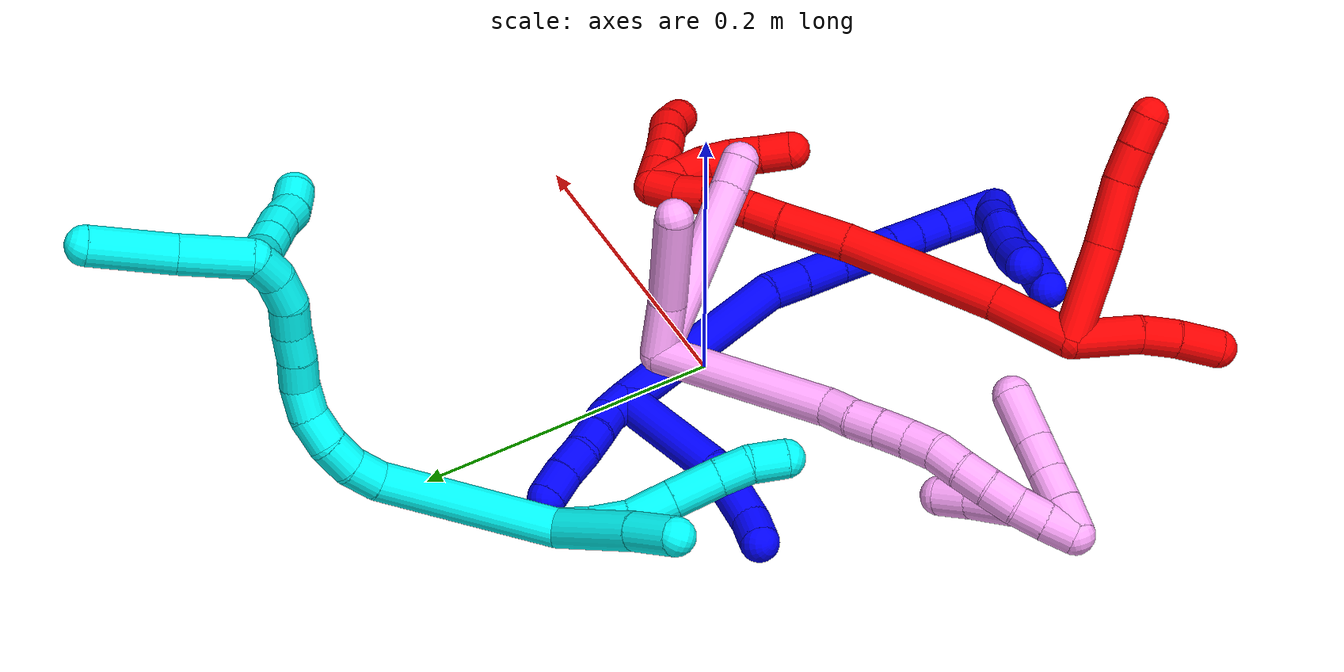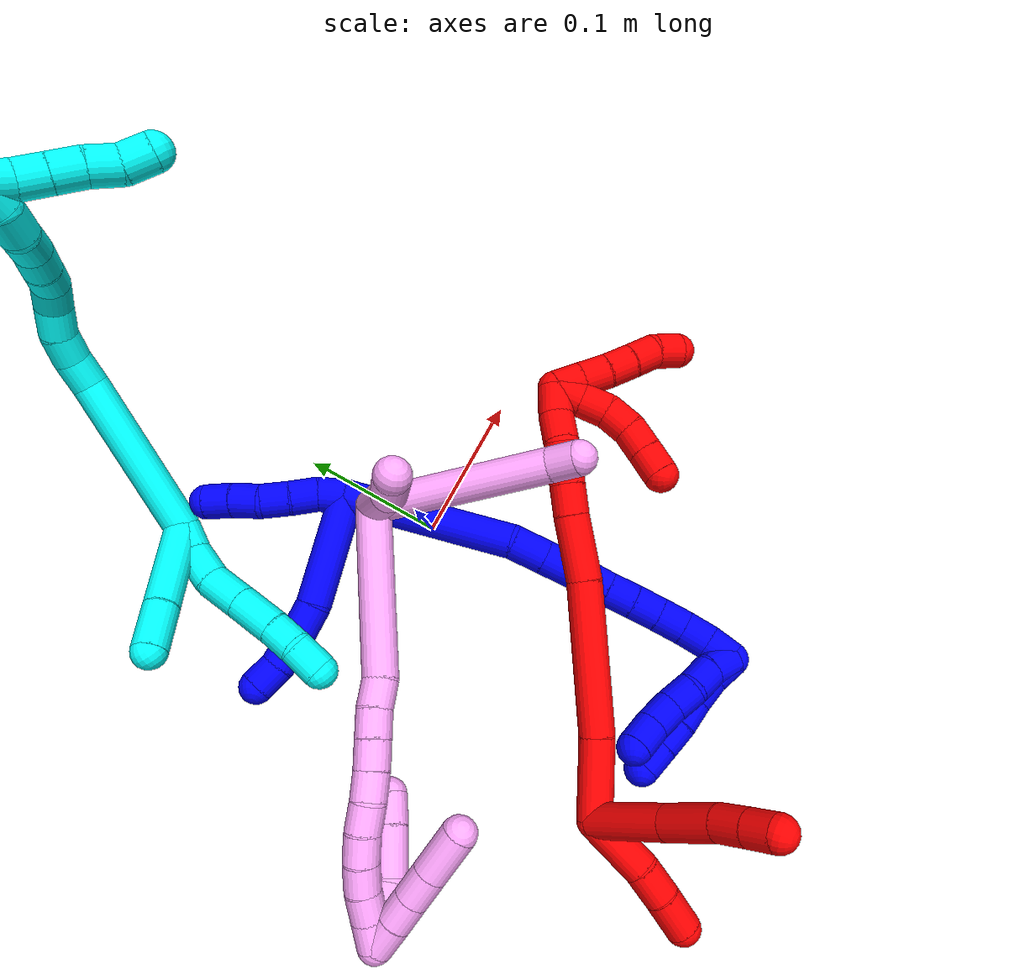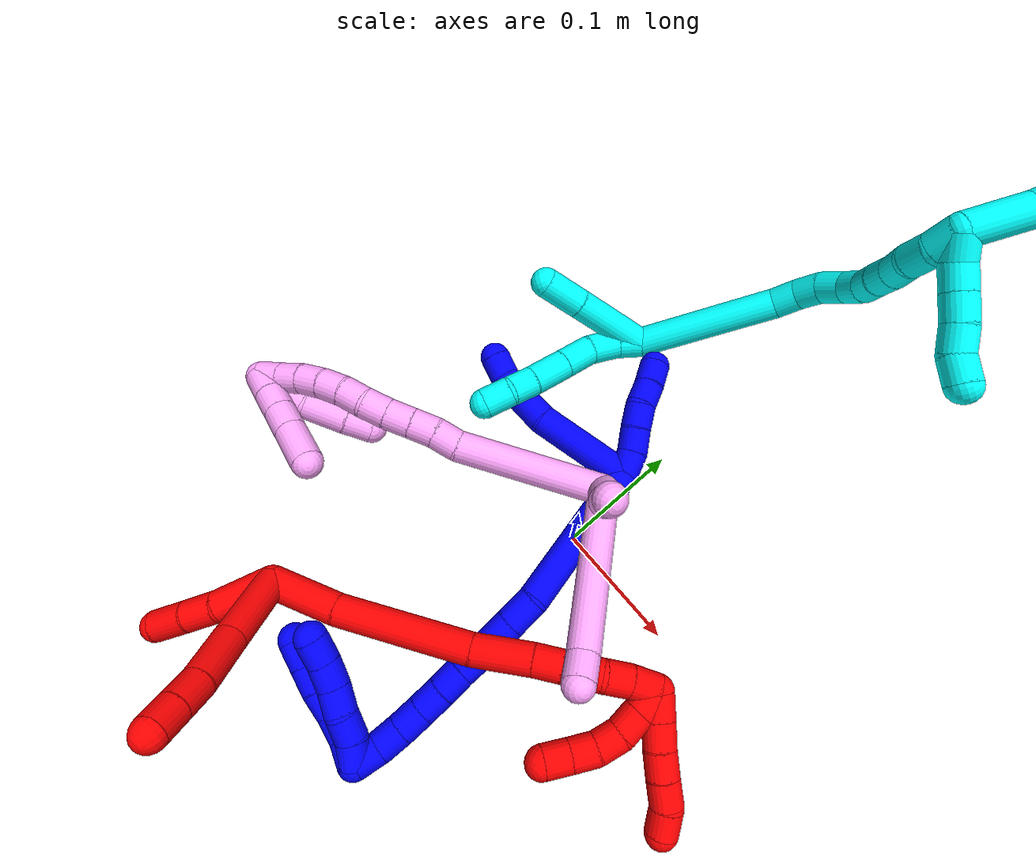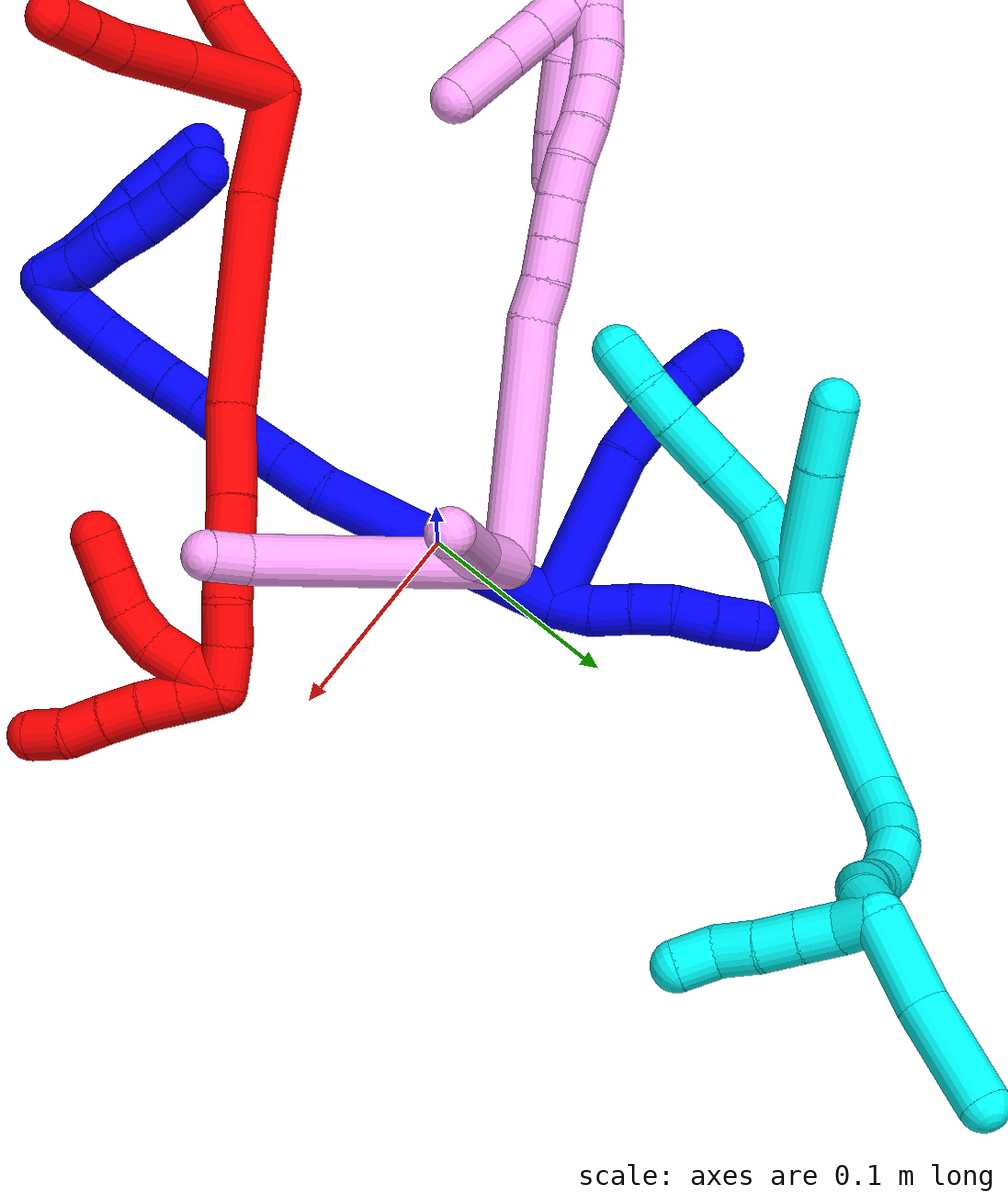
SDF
<sdf version="1.7">
 <world name="default">
  <plugin name="TubeGeneratorPlugin" filename="libtube_generator_plugin.so"/>
  <model name="photoneo_s_sensor">
   <static>1</static>
   <pose>0 0 2 1.57079 1.57079 3.14159</pose>
   <link name="link">
    <inertial><mass>0.1</mass></inertial>
    <sensor name="sensor" type="depth">
     <update_rate>30</update_rate>
     <camera>
      <horizontal_fov>1.22</horizontal_fov>
      <image><width>1920</width><height>1200</height><format>B8G8R8</format></image>
      <clip><near>0.1</near><far>4</far></clip>
      <depth_camera><output>points</output></depth_camera>
     </camera>
     <plugin name="camera_plugin" filename="libgazebo_ros_depth_camera.so">
      <baseline>0.2</baseline>
      <alwaysOn>1</alwaysOn>
      <updateRate>0.0</updateRate>
      <cameraName>camera_ir</cameraName>
      <imageTopicName>/camera/color/image_raw</imageTopicName>
      <cameraInfoTopicName>/camera/color/camera_info</cameraInfoTopicName>
      <depthImageTopicName>/camera/depth/image_raw</depthImageTopicName>
      <depthImageCameraInfoTopicName>/camera/depth/camera_info</depthImageCameraInfoTopicName>
      <pointCloudTopicName>/camera/depth/points</pointCloudTopicName>
      <frameName>fr_optical</frameName>
      <pointCloudCutoff>0.1</pointCloudCutoff>
      <pointCloudCutoffMax>2.0</pointCloudCutoffMax>
      <distortionK1>0</distortionK1>
      <distortionK2>0</distortionK2>
      <distortionK3>0</distortionK3>
      <distortionT1>0</distortionT1>
      <distortionT2>0</distortionT2>
      <CxPrime>0</CxPrime>
      <Cx>0</Cx>
      <Cy>0</Cy>
      <focalLength>0</focalLength>
      <hackBaseline>0</hackBaseline>
     </plugin>
    </sensor>
   </link>
  </model>
  <gravity>0 0 -9.8</gravity>
  <magnetic_field>6e-06 2.3e-05 -4.2e-05</magnetic_field>
  <atmosphere type="adiabatic"/>
  <physics name="default_physics" default="0" type="ode">
   <max_step_size>0.003</max_step_size>
   <real_time_factor>1</real_time_factor>
   <real_time_update_rate>1000</real_time_update_rate>
   <max_contacts>10000</max_contacts>
   <ode>
    <solver>
     <type>quick</type>
     <iters>100</iters>
     <sor>1.3</sor>
     <use_dynamic_moi_rescaling>0</use_dynamic_moi_rescaling>
    </solver>
    <constraints>
     <contact_max_correcting_vel>0</contact_max_correcting_vel>
     <contact_surface_layer>0.001</contact_surface_layer>
     <cfm>0</cfm>
     <erp>0.2</erp>
    </constraints>
   </ode>
  </physics>
  <scene><ambient>0.4 0.4 0.4 1</ambient><background>0.7 0.7 0.7 1</background><shadows>0</shadows></scene>
  <audio><device>default</device></audio>
  <spherical_coordinates>
   <surface_model>EARTH_WGS84</surface_model>
   <latitude_deg>0</latitude_deg>
   <longitude_deg>0</longitude_deg>
   <elevation>0</elevation>
   <heading_deg>0</heading_deg>
  </spherical_coordinates>
  <model name="bin">
   <static>1</static>
   <link name="bottom">
    <collision name="collision-bottom">
     <pose>0 0 -0.01 0 -0 0</pose>
     <geometry><box><size>0.8 0.6 0.02</size></box></geometry>
     <surface>
      <friction><ode><mu>100</mu><mu2>100</mu2></ode></friction>
      <contact><collide_bitmask>65535</collide_bitmask></contact>
     </surface>
    </collision>
   </link>
   <link name="west_wall">
    <collision name="collision-west_wall">
     <pose>-0.41 0 0.1 0 -0 0</pose>
     <geometry><box><size>0.02 0.6 0.2</size></box></geometry>
     <surface>
      <friction><ode><mu>100</mu><mu2>100</mu2></ode></friction>
      <contact><collide_bitmask>65535</collide_bitmask></contact>
     </surface>
    </collision>
   </link>
   <link name="east_wall">
    <collision name="collision-east_wall">
     <pose>0.41 0 0.1 0 -0 0</pose>
     <geometry><box><size>0.02 0.6 0.2</size></box></geometry>
     <surface>
      <friction><ode><mu>100</mu><mu2>100</mu2></ode></friction>
      <contact><collide_bitmask>65535</collide_bitmask></contact>
     </surface>
    </collision>
   </link>
   <link name="south_wall">
    <collision name="collision-south_wall">
     <pose>0 -0.31 0.1 0 -0 0</pose>
     <geometry><box><size>0.8 0.02 0.2</size></box></geometry>
     <surface>
      <friction><ode><mu>100</mu><mu2>100</mu2></ode></friction>
      <contact><collide_bitmask>65535</collide_bitmask></contact>
     </surface>
    </collision>
   </link>
   <link name="north_wall">
    <collision name="collision-north_wall">
     <pose>0 0.31 0.1 0 -0 0</pose>
     <geometry><box><size>0.8 0.02 0.2</size></box></geometry>
     <surface>
      <friction><ode><mu>100</mu><mu2>100</mu2></ode></friction>
      <contact><collide_bitmask>65535</collide_bitmask></contact>
     </surface>
    </collision>
   </link>
  </model>
  <model name="1">
   <static>0</static>
   <link name="1">
    <collision name="collision-cylinder-e_1_2_8">
     <pose>-0.020403 -0.000506 0.034634 0.014619 -0.532313 -0.003986</pose>
     <geometry><cylinder><radius>0.0125</radius><length>0.0804</length></cylinder></geometry>
     <surface>
      <friction><ode><mu>1.16</mu><mu2>1.16</mu2><slip1>0</slip1><slip2>0</slip2></ode></friction>
      <contact><ode><kp>1e+06</kp><kd>1</kd><max_vel>0</max_vel><min_depth>0.001</min_depth></ode></contact>
     </surface>
    </collision>
    <visual name="visual-cylinder-e_1_2_8">
     <pose>-0.020403 -0.000506 0.034634 0.014619 -0.532313 -0.003986</pose>
     <geometry><cylinder><radius>0.0125</radius><length>0.0804</length></cylinder></geometry>
     <material><ambient>0 0 1 1</ambient></material>
    </visual>
    <collision name="collision-cylinder-e_2_8_9">
     <pose>-0.048115 0.001256 0.078855 -0.232407 -0.638393 0.077119</pose>
     <geometry><cylinder><radius>0.0125</radius><length>0.024535</length></cylinder></geometry>
     <surface>
      <friction><ode><mu>1.16</mu><mu2>1.16</mu2><slip1>0</slip1><slip2>0</slip2></ode></friction>
      <contact><ode><kp>1e+06</kp><kd>1</kd><max_vel>0</max_vel><min_depth>0.001</min_depth></ode></contact>
     </surface>
    </collision>
    <visual name="visual-cylinder-e_2_8_9">
     <pose>-0.048115 0.001256 0.078855 -0.232407 -0.638393 0.077119</pose>
     <geometry><cylinder><radius>0.0125</radius><length>0.024535</length></cylinder></geometry>
     <material><ambient>0 0 1 1</ambient></material>
    </visual>
    <collision name="collision-cylinder-e_3_9_10">
     <pose>-0.062956 0.00676 0.097839 -0.331517 -0.648421 0.112326</pose>
     <geometry><cylinder><radius>0.0125</radius><length>0.024939</length></cylinder></geometry>
     <surface>
      <friction><ode><mu>1.16</mu><mu2>1.16</mu2><slip1>0</slip1><slip2>0</slip2></ode></friction>
      <contact><ode><kp>1e+06</kp><kd>1</kd><max_vel>0</max_vel><min_depth>0.001</min_depth></ode></contact>
     </surface>
    </collision>
    <visual name="visual-cylinder-e_3_9_10">
     <pose>-0.062956 0.00676 0.097839 -0.331517 -0.648421 0.112326</pose>
     <geometry><cylinder><radius>0.0125</radius><length>0.024939</length></cylinder></geometry>
     <material><ambient>0 0 1 1</ambient></material>
    </visual>
    <collision name="collision-cylinder-e_4_10_6">
     <pose>-0.075039 0.01472 0.114866 -0.55452 -0.469376 0.135878</pose>
     <geometry><cylinder><radius>0.0125</radius><length>0.020127</length></cylinder></geometry>
     <surface>
      <friction><ode><mu>1.16</mu><mu2>1.16</mu2><slip1>0</slip1><slip2>0</slip2></ode></friction>
      <contact><ode><kp>1e+06</kp><kd>1</kd><max_vel>0</max_vel><min_depth>0.001</min_depth></ode></contact>
     </surface>
    </collision>
    <visual name="visual-cylinder-e_4_10_6">
     <pose>-0.075039 0.01472 0.114866 -0.55452 -0.469376 0.135878</pose>
     <geometry><cylinder><radius>0.0125</radius><length>0.020127</length></cylinder></geometry>
     <material><ambient>0 0 1 1</ambient></material>
    </visual>
    <collision name="collision-cylinder-e_1_2_11">
     <pose>-0.001843 0.009742 0.001303 -1.4378 -0.185399 0.162356</pose>
     <geometry><cylinder><radius>0.0125</radius><length>0.02</length></cylinder></geometry>
     <surface>
      <friction><ode><mu>1.16</mu><mu2>1.16</mu2><slip1>0</slip1><slip2>0</slip2></ode></friction>
      <contact><ode><kp>1e+06</kp><kd>1</kd><max_vel>0</max_vel><min_depth>0.001</min_depth></ode></contact>
     </surface>
    </collision>
    <visual name="visual-cylinder-e_1_2_11">
     <pose>-0.001843 0.009742 0.001303 -1.4378 -0.185399 0.162356</pose>
     <geometry><cylinder><radius>0.0125</radius><length>0.02</length></cylinder></geometry>
     <material><ambient>0 0 1 1</ambient></material>
    </visual>
    <collision name="collision-cylinder-e_2_11_12">
     <pose>-0.005834 0.028426 0.006534 -1.15694 -0.216404 0.141625</pose>
     <geometry><cylinder><radius>0.0125</radius><length>0.02</length></cylinder></geometry>
     <surface>
      <friction><ode><mu>1.16</mu><mu2>1.16</mu2><slip1>0</slip1><slip2>0</slip2></ode></friction>
      <contact><ode><kp>1e+06</kp><kd>1</kd><max_vel>0</max_vel><min_depth>0.001</min_depth></ode></contact>
     </surface>
    </collision>
    <visual name="visual-cylinder-e_2_11_12">
     <pose>-0.005834 0.028426 0.006534 -1.15694 -0.216404 0.141625</pose>
     <geometry><cylinder><radius>0.0125</radius><length>0.02</length></cylinder></geometry>
     <material><ambient>0 0 1 1</ambient></material>
    </visual>
    <collision name="collision-cylinder-e_3_12_13">
     <pose>-0.010697 0.046539 0.013381 -1.26263 -0.275074 0.201707</pose>
     <geometry><cylinder><radius>0.0125</radius><length>0.02</length></cylinder></geometry>
     <surface>
      <friction><ode><mu>1.16</mu><mu2>1.16</mu2><slip1>0</slip1><slip2>0</slip2></ode></friction>
      <contact><ode><kp>1e+06</kp><kd>1</kd><max_vel>0</max_vel><min_depth>0.001</min_depth></ode></contact>
     </surface>
    </collision>
    <visual name="visual-cylinder-e_3_12_13">
     <pose>-0.010697 0.046539 0.013381 -1.26263 -0.275074 0.201707</pose>
     <geometry><cylinder><radius>0.0125</radius><length>0.02</length></cylinder></geometry>
     <material><ambient>0 0 1 1</ambient></material>
    </visual>
    <collision name="collision-cylinder-e_4_13_14">
     <pose>-0.017148 0.064981 0.016591 -1.53946 -0.38272 0.371185</pose>
     <geometry><cylinder><radius>0.0125</radius><length>0.02</length></cylinder></geometry>
     <surface>
      <friction><ode><mu>1.16</mu><mu2>1.16</mu2><slip1>0</slip1><slip2>0</slip2></ode></friction>
      <contact><ode><kp>1e+06</kp><kd>1</kd><max_vel>0</max_vel><min_depth>0.001</min_depth></ode></contact>
     </surface>
    </collision>
    <visual name="visual-cylinder-e_4_13_14">
     <pose>-0.017148 0.064981 0.016591 -1.53946 -0.38272 0.371185</pose>
     <geometry><cylinder><radius>0.0125</radius><length>0.02</length></cylinder></geometry>
     <material><ambient>0 0 1 1</ambient></material>
    </visual>
    <collision name="collision-cylinder-e_5_14_5">
     <pose>-0.025411 0.083127 0.017745 -1.47381 -0.469951 0.427826</pose>
     <geometry><cylinder><radius>0.0125</radius><length>0.02</length></cylinder></geometry>
     <surface>
      <friction><ode><mu>1.16</mu><mu2>1.16</mu2><slip1>0</slip1><slip2>0</slip2></ode></friction>
      <contact><ode><kp>1e+06</kp><kd>1</kd><max_vel>0</max_vel><min_depth>0.001</min_depth></ode></contact>
     </surface>
    </collision>
    <visual name="visual-cylinder-e_5_14_5">
     <pose>-0.025411 0.083127 0.017745 -1.47381 -0.469951 0.427826</pose>
     <geometry><cylinder><radius>0.0125</radius><length>0.02</length></cylinder></geometry>
     <material><ambient>0 0 1 1</ambient></material>
    </visual>
    <collision name="collision-cylinder-e_1_2_15">
     <pose>0.016047 -0.059596 0.009551 1.41189 0.259863 0.221874</pose>
     <geometry><cylinder><radius>0.0125</radius><length>0.124906</length></cylinder></geometry>
     <surface>
      <friction><ode><mu>1.16</mu><mu2>1.16</mu2><slip1>0</slip1><slip2>0</slip2></ode></friction>
      <contact><ode><kp>1e+06</kp><kd>1</kd><max_vel>0</max_vel><min_depth>0.001</min_depth></ode></contact>
     </surface>
    </collision>
    <visual name="visual-cylinder-e_1_2_15">
     <pose>0.016047 -0.059596 0.009551 1.41189 0.259863 0.221874</pose>
     <geometry><cylinder><radius>0.0125</radius><length>0.124906</length></cylinder></geometry>
     <material><ambient>0 0 1 1</ambient></material>
    </visual>
    <collision name="collision-cylinder-e_2_15_16">
     <pose>0.031978 -0.131523 0.021443 1.38313 -0.009261 -0.007668</pose>
     <geometry><cylinder><radius>0.0125</radius><length>0.025104</length></cylinder></geometry>
     <surface>
      <friction><ode><mu>1.16</mu><mu2>1.16</mu2><slip1>0</slip1><slip2>0</slip2></ode></friction>
      <contact><ode><kp>1e+06</kp><kd>1</kd><max_vel>0</max_vel><min_depth>0.001</min_depth></ode></contact>
     </surface>
    </collision>
    <visual name="visual-cylinder-e_2_15_16">
     <pose>0.031978 -0.131523 0.021443 1.38313 -0.009261 -0.007668</pose>
     <geometry><cylinder><radius>0.0125</radius><length>0.025104</length></cylinder></geometry>
     <material><ambient>0 0 1 1</ambient></material>
    </visual>
    <collision name="collision-cylinder-e_3_16_17">
     <pose>0.031949 -0.158205 0.026521 1.38239 0.005948 0.004921</pose>
     <geometry><cylinder><radius>0.0125</radius><length>0.029221</length></cylinder></geometry>
     <surface>
      <friction><ode><mu>1.16</mu><mu2>1.16</mu2><slip1>0</slip1><slip2>0</slip2></ode></friction>
      <contact><ode><kp>1e+06</kp><kd>1</kd><max_vel>0</max_vel><min_depth>0.001</min_depth></ode></contact>
     </surface>
    </collision>
    <visual name="visual-cylinder-e_3_16_17">
     <pose>0.031949 -0.158205 0.026521 1.38239 0.005948 0.004921</pose>
     <geometry><cylinder><radius>0.0125</radius><length>0.029221</length></cylinder></geometry>
     <material><ambient>0 0 1 1</ambient></material>
    </visual>
    <collision name="collision-cylinder-e_4_17_18">
     <pose>0.032206 -0.182491 0.031924 1.30848 0.016575 0.012712</pose>
     <geometry><cylinder><radius>0.0125</radius><length>0.020574</length></cylinder></geometry>
     <surface>
      <friction><ode><mu>1.16</mu><mu2>1.16</mu2><slip1>0</slip1><slip2>0</slip2></ode></friction>
      <contact><ode><kp>1e+06</kp><kd>1</kd><max_vel>0</max_vel><min_depth>0.001</min_depth></ode></contact>
     </surface>
    </collision>
    <visual name="visual-cylinder-e_4_17_18">
     <pose>0.032206 -0.182491 0.031924 1.30848 0.016575 0.012712</pose>
     <geometry><cylinder><radius>0.0125</radius><length>0.020574</length></cylinder></geometry>
     <material><ambient>0 0 1 1</ambient></material>
    </visual>
    <collision name="collision-cylinder-e_5_18_19">
     <pose>0.032607 -0.202249 0.036645 1.36475 0.022896 0.018605</pose>
     <geometry><cylinder><radius>0.0125</radius><length>0.020079</length></cylinder></geometry>
     <surface>
      <friction><ode><mu>1.16</mu><mu2>1.16</mu2><slip1>0</slip1><slip2>0</slip2></ode></friction>
      <contact><ode><kp>1e+06</kp><kd>1</kd><max_vel>0</max_vel><min_depth>0.001</min_depth></ode></contact>
     </surface>
    </collision>
    <visual name="visual-cylinder-e_5_18_19">
     <pose>0.032607 -0.202249 0.036645 1.36475 0.022896 0.018605</pose>
     <geometry><cylinder><radius>0.0125</radius><length>0.020079</length></cylinder></geometry>
     <material><ambient>0 0 1 1</ambient></material>
    </visual>
    <collision name="collision-cylinder-e_6_19_20">
     <pose>0.03274 -0.221867 0.040812 1.3583 -0.009628 -0.007772</pose>
     <geometry><cylinder><radius>0.0125</radius><length>0.020037</length></cylinder></geometry>
     <surface>
      <friction><ode><mu>1.16</mu><mu2>1.16</mu2><slip1>0</slip1><slip2>0</slip2></ode></friction>
      <contact><ode><kp>1e+06</kp><kd>1</kd><max_vel>0</max_vel><min_depth>0.001</min_depth></ode></contact>
     </surface>
    </collision>
    <visual name="visual-cylinder-e_6_19_20">
     <pose>0.03274 -0.221867 0.040812 1.3583 -0.009628 -0.007772</pose>
     <geometry><cylinder><radius>0.0125</radius><length>0.020037</length></cylinder></geometry>
     <material><ambient>0 0 1 1</ambient></material>
    </visual>
    <collision name="collision-cylinder-e_7_20_21">
     <pose>0.032816 -0.24134 0.04543 1.31754 0.017218 0.013329</pose>
     <geometry><cylinder><radius>0.0125</radius><length>0.020002</length></cylinder></geometry>
     <surface>
      <friction><ode><mu>1.16</mu><mu2>1.16</mu2><slip1>0</slip1><slip2>0</slip2></ode></friction>
      <contact><ode><kp>1e+06</kp><kd>1</kd><max_vel>0</max_vel><min_depth>0.001</min_depth></ode></contact>
     </surface>
    </collision>
    <visual name="visual-cylinder-e_7_20_21">
     <pose>0.032816 -0.24134 0.04543 1.31754 0.017218 0.013329</pose>
     <geometry><cylinder><radius>0.0125</radius><length>0.020002</length></cylinder></geometry>
     <material><ambient>0 0 1 1</ambient></material>
    </visual>
    <collision name="collision-cylinder-e_8_21_22">
     <pose>0.033185 -0.260536 0.051005 1.25876 0.019733 0.014369</pose>
     <geometry><cylinder><radius>0.0125</radius><length>0.02</length></cylinder></geometry>
     <surface>
      <friction><ode><mu>1.16</mu><mu2>1.16</mu2><slip1>0</slip1><slip2>0</slip2></ode></friction>
      <contact><ode><kp>1e+06</kp><kd>1</kd><max_vel>0</max_vel><min_depth>0.001</min_depth></ode></contact>
     </surface>
    </collision>
    <visual name="visual-cylinder-e_8_21_22">
     <pose>0.033185 -0.260536 0.051005 1.25876 0.019733 0.014369</pose>
     <geometry><cylinder><radius>0.0125</radius><length>0.02</length></cylinder></geometry>
     <material><ambient>0 0 1 1</ambient></material>
    </visual>
    <collision name="collision-cylinder-e_9_22_1">
     <pose>0.034089 -0.278899 0.058763 1.08345 0.070425 0.042392</pose>
     <geometry><cylinder><radius>0.0125</radius><length>0.020077</length></cylinder></geometry>
     <surface>
      <friction><ode><mu>1.16</mu><mu2>1.16</mu2><slip1>0</slip1><slip2>0</slip2></ode></friction>
      <contact><ode><kp>1e+06</kp><kd>1</kd><max_vel>0</max_vel><min_depth>0.001</min_depth></ode></contact>
     </surface>
    </collision>
    <visual name="visual-cylinder-e_9_22_1">
     <pose>0.034089 -0.278899 0.058763 1.08345 0.070425 0.042392</pose>
     <geometry><cylinder><radius>0.0125</radius><length>0.020077</length></cylinder></geometry>
     <material><ambient>0 0 1 1</ambient></material>
    </visual>
    <collision name="collision-cylinder-e_1_1_23">
     <pose>0.033825 -0.280256 0.070007 -0.851952 -0.097125 0.044099</pose>
     <geometry><cylinder><radius>0.0125</radius><length>0.02</length></cylinder></geometry>
     <surface>
      <friction><ode><mu>1.16</mu><mu2>1.16</mu2><slip1>0</slip1><slip2>0</slip2></ode></friction>
      <contact><ode><kp>1e+06</kp><kd>1</kd><max_vel>0</max_vel><min_depth>0.001</min_depth></ode></contact>
     </surface>
    </collision>
    <visual name="visual-cylinder-e_1_1_23">
     <pose>0.033825 -0.280256 0.070007 -0.851952 -0.097125 0.044099</pose>
     <geometry><cylinder><radius>0.0125</radius><length>0.02</length></cylinder></geometry>
     <material><ambient>0 0 1 1</ambient></material>
    </visual>
    <collision name="collision-cylinder-e_2_23_24">
     <pose>0.031686 -0.267267 0.084831 -0.586759 -0.11722 0.035449</pose>
     <geometry><cylinder><radius>0.0125</radius><length>0.02</length></cylinder></geometry>
     <surface>
      <friction><ode><mu>1.16</mu><mu2>1.16</mu2><slip1>0</slip1><slip2>0</slip2></ode></friction>
      <contact><ode><kp>1e+06</kp><kd>1</kd><max_vel>0</max_vel><min_depth>0.001</min_depth></ode></contact>
     </surface>
    </collision>
    <visual name="visual-cylinder-e_2_23_24">
     <pose>0.031686 -0.267267 0.084831 -0.586759 -0.11722 0.035449</pose>
     <geometry><cylinder><radius>0.0125</radius><length>0.02</length></cylinder></geometry>
     <material><ambient>0 0 1 1</ambient></material>
    </visual>
    <collision name="collision-cylinder-e_3_24_25">
     <pose>0.027037 -0.255747 0.100287 -0.697423 -0.35538 0.130397</pose>
     <geometry><cylinder><radius>0.0125</radius><length>0.02</length></cylinder></geometry>
     <surface>
      <friction><ode><mu>1.16</mu><mu2>1.16</mu2><slip1>0</slip1><slip2>0</slip2></ode></friction>
      <contact><ode><kp>1e+06</kp><kd>1</kd><max_vel>0</max_vel><min_depth>0.001</min_depth></ode></contact>
     </surface>
    </collision>
    <visual name="visual-cylinder-e_3_24_25">
     <pose>0.027037 -0.255747 0.100287 -0.697423 -0.35538 0.130397</pose>
     <geometry><cylinder><radius>0.0125</radius><length>0.02</length></cylinder></geometry>
     <material><ambient>0 0 1 1</ambient></material>
    </visual>
    <collision name="collision-cylinder-e_4_25_26">
     <pose>0.02141 -0.244299 0.115593 -0.589147 -0.216457 0.065907</pose>
     <geometry><cylinder><radius>0.0125</radius><length>0.02</length></cylinder></geometry>
     <surface>
      <friction><ode><mu>1.16</mu><mu2>1.16</mu2><slip1>0</slip1><slip2>0</slip2></ode></friction>
      <contact><ode><kp>1e+06</kp><kd>1</kd><max_vel>0</max_vel><min_depth>0.001</min_depth></ode></contact>
     </surface>
    </collision>
    <visual name="visual-cylinder-e_4_25_26">
     <pose>0.02141 -0.244299 0.115593 -0.589147 -0.216457 0.065907</pose>
     <geometry><cylinder><radius>0.0125</radius><length>0.02</length></cylinder></geometry>
     <material><ambient>0 0 1 1</ambient></material>
    </visual>
    <collision name="collision-cylinder-e_5_26_4">
     <pose>0.017856 -0.234174 0.132428 -0.494508 -0.141138 0.035681</pose>
     <geometry><cylinder><radius>0.0125</radius><length>0.02</length></cylinder></geometry>
     <surface>
      <friction><ode><mu>1.16</mu><mu2>1.16</mu2><slip1>0</slip1><slip2>0</slip2></ode></friction>
      <contact><ode><kp>1e+06</kp><kd>1</kd><max_vel>0</max_vel><min_depth>0.001</min_depth></ode></contact>
     </surface>
    </collision>
    <visual name="visual-cylinder-e_5_26_4">
     <pose>0.017856 -0.234174 0.132428 -0.494508 -0.141138 0.035681</pose>
     <geometry><cylinder><radius>0.0125</radius><length>0.02</length></cylinder></geometry>
     <material><ambient>0 0 1 1</ambient></material>
    </visual>
    <collision name="collision-cylinder-e_1_1_27">
     <pose>0.030849 -0.282068 0.070676 -0.666131 -0.405688 0.142067</pose>
     <geometry><cylinder><radius>0.0125</radius><length>0.02</length></cylinder></geometry>
     <surface>
      <friction><ode><mu>1.16</mu><mu2>1.16</mu2><slip1>0</slip1><slip2>0</slip2></ode></friction>
      <contact><ode><kp>1e+06</kp><kd>1</kd><max_vel>0</max_vel><min_depth>0.001</min_depth></ode></contact>
     </surface>
    </collision>
    <visual name="visual-cylinder-e_1_1_27">
     <pose>0.030849 -0.282068 0.070676 -0.666131 -0.405688 0.142067</pose>
     <geometry><cylinder><radius>0.0125</radius><length>0.02</length></cylinder></geometry>
     <material><ambient>0 0 1 1</ambient></material>
    </visual>
    <collision name="collision-cylinder-e_2_27_28">
     <pose>0.022176 -0.272495 0.085805 -0.45787 -0.492311 0.11696</pose>
     <geometry><cylinder><radius>0.0125</radius><length>0.02</length></cylinder></geometry>
     <surface>
      <friction><ode><mu>1.16</mu><mu2>1.16</mu2><slip1>0</slip1><slip2>0</slip2></ode></friction>
      <contact><ode><kp>1e+06</kp><kd>1</kd><max_vel>0</max_vel><min_depth>0.001</min_depth></ode></contact>
     </surface>
    </collision>
    <visual name="visual-cylinder-e_2_27_28">
     <pose>0.022176 -0.272495 0.085805 -0.45787 -0.492311 0.11696</pose>
     <geometry><cylinder><radius>0.0125</radius><length>0.02</length></cylinder></geometry>
     <material><ambient>0 0 1 1</ambient></material>
    </visual>
    <collision name="collision-cylinder-e_3_28_29">
     <pose>0.013779 -0.265099 0.102328 -0.385858 -0.375788 0.074256</pose>
     <geometry><cylinder><radius>0.0125</radius><length>0.02</length></cylinder></geometry>
     <surface>
      <friction><ode><mu>1.16</mu><mu2>1.16</mu2><slip1>0</slip1><slip2>0</slip2></ode></friction>
      <contact><ode><kp>1e+06</kp><kd>1</kd><max_vel>0</max_vel><min_depth>0.001</min_depth></ode></contact>
     </surface>
    </collision>
    <visual name="visual-cylinder-e_3_28_29">
     <pose>0.013779 -0.265099 0.102328 -0.385858 -0.375788 0.074256</pose>
     <geometry><cylinder><radius>0.0125</radius><length>0.02</length></cylinder></geometry>
     <material><ambient>0 0 1 1</ambient></material>
    </visual>
    <collision name="collision-cylinder-e_4_29_30">
     <pose>0.006417 -0.257029 0.119039 -0.513997 -0.378157 0.100501</pose>
     <geometry><cylinder><radius>0.0125</radius><length>0.02</length></cylinder></geometry>
     <surface>
      <friction><ode><mu>1.16</mu><mu2>1.16</mu2><slip1>0</slip1><slip2>0</slip2></ode></friction>
      <contact><ode><kp>1e+06</kp><kd>1</kd><max_vel>0</max_vel><min_depth>0.001</min_depth></ode></contact>
     </surface>
    </collision>
    <visual name="visual-cylinder-e_4_29_30">
     <pose>0.006417 -0.257029 0.119039 -0.513997 -0.378157 0.100501</pose>
     <geometry><cylinder><radius>0.0125</radius><length>0.02</length></cylinder></geometry>
     <material><ambient>0 0 1 1</ambient></material>
    </visual>
    <collision name="collision-cylinder-e_5_30_3">
     <pose>-0.000943 -0.247873 0.135226 -0.515518 -0.375566 0.100105</pose>
     <geometry><cylinder><radius>0.0125</radius><length>0.02</length></cylinder></geometry>
     <surface>
      <friction><ode><mu>1.16</mu><mu2>1.16</mu2><slip1>0</slip1><slip2>0</slip2></ode></friction>
      <contact><ode><kp>1e+06</kp><kd>1</kd><max_vel>0</max_vel><min_depth>0.001</min_depth></ode></contact>
     </surface>
    </collision>
    <visual name="visual-cylinder-e_5_30_3">
     <pose>-0.000943 -0.247873 0.135226 -0.515518 -0.375566 0.100105</pose>
     <geometry><cylinder><radius>0.0125</radius><length>0.02</length></cylinder></geometry>
     <material><ambient>0 0 1 1</ambient></material>
    </visual>
    <collision name="collision-sphere-3">
     <pose>-0.004611 -0.243287 0.14332 0 -0 0</pose>
     <geometry><sphere><radius>0.0125</radius></sphere></geometry>
     <surface>
      <friction><ode><mu>1.16</mu><mu2>1.16</mu2><slip1>0</slip1><slip2>0</slip2></ode></friction>
      <contact><ode><kp>1e+06</kp><kd>1</kd><max_vel>0</max_vel><min_depth>0.001</min_depth></ode></contact>
     </surface>
    </collision>
    <visual name="visual-sphere-3">
     <pose>-0.004611 -0.243287 0.14332 0 -0 0</pose>
     <geometry><sphere><radius>0.0125</radius></sphere></geometry>
     <material><ambient>0 0 1 1</ambient></material>
    </visual>
    <collision name="collision-sphere-30">
     <pose>0.002725 -0.252459 0.127132 0 -0 0</pose>
     <geometry><sphere><radius>0.0125</radius></sphere></geometry>
     <surface>
      <friction><ode><mu>1.16</mu><mu2>1.16</mu2><slip1>0</slip1><slip2>0</slip2></ode></friction>
      <contact><ode><kp>1e+06</kp><kd>1</kd><max_vel>0</max_vel><min_depth>0.001</min_depth></ode></contact>
     </surface>
    </collision>
    <visual name="visual-sphere-30">
     <pose>0.002725 -0.252459 0.127132 0 -0 0</pose>
     <geometry><sphere><radius>0.0125</radius></sphere></geometry>
     <material><ambient>0 0 1 1</ambient></material>
    </visual>
    <collision name="collision-sphere-29">
     <pose>0.010109 -0.261598 0.110946 0 -0 0</pose>
     <geometry><sphere><radius>0.0125</radius></sphere></geometry>
     <surface>
      <friction><ode><mu>1.16</mu><mu2>1.16</mu2><slip1>0</slip1><slip2>0</slip2></ode></friction>
      <contact><ode><kp>1e+06</kp><kd>1</kd><max_vel>0</max_vel><min_depth>0.001</min_depth></ode></contact>
     </surface>
    </collision>
    <visual name="visual-sphere-29">
     <pose>0.010109 -0.261598 0.110946 0 -0 0</pose>
     <geometry><sphere><radius>0.0125</radius></sphere></geometry>
     <material><ambient>0 0 1 1</ambient></material>
    </visual>
    <collision name="collision-sphere-28">
     <pose>0.017449 -0.2686 0.09371 0 -0 0</pose>
     <geometry><sphere><radius>0.0125</radius></sphere></geometry>
     <surface>
      <friction><ode><mu>1.16</mu><mu2>1.16</mu2><slip1>0</slip1><slip2>0</slip2></ode></friction>
      <contact><ode><kp>1e+06</kp><kd>1</kd><max_vel>0</max_vel><min_depth>0.001</min_depth></ode></contact>
     </surface>
    </collision>
    <visual name="visual-sphere-28">
     <pose>0.017449 -0.2686 0.09371 0 -0 0</pose>
     <geometry><sphere><radius>0.0125</radius></sphere></geometry>
     <material><ambient>0 0 1 1</ambient></material>
    </visual>
    <collision name="collision-sphere-27">
     <pose>0.026902 -0.276391 0.0779 0 -0 0</pose>
     <geometry><sphere><radius>0.0125</radius></sphere></geometry>
     <surface>
      <friction><ode><mu>1.16</mu><mu2>1.16</mu2><slip1>0</slip1><slip2>0</slip2></ode></friction>
      <contact><ode><kp>1e+06</kp><kd>1</kd><max_vel>0</max_vel><min_depth>0.001</min_depth></ode></contact>
     </surface>
    </collision>
    <visual name="visual-sphere-27">
     <pose>0.026902 -0.276391 0.0779 0 -0 0</pose>
     <geometry><sphere><radius>0.0125</radius></sphere></geometry>
     <material><ambient>0 0 1 1</ambient></material>
    </visual>
    <collision name="collision-sphere-4">
     <pose>0.016449 -0.229475 0.141143 0 -0 0</pose>
     <geometry><sphere><radius>0.0125</radius></sphere></geometry>
     <surface>
      <friction><ode><mu>1.16</mu><mu2>1.16</mu2><slip1>0</slip1><slip2>0</slip2></ode></friction>
      <contact><ode><kp>1e+06</kp><kd>1</kd><max_vel>0</max_vel><min_depth>0.001</min_depth></ode></contact>
     </surface>
    </collision>
    <visual name="visual-sphere-4">
     <pose>0.016449 -0.229475 0.141143 0 -0 0</pose>
     <geometry><sphere><radius>0.0125</radius></sphere></geometry>
     <material><ambient>0 0 1 1</ambient></material>
    </visual>
    <collision name="collision-sphere-26">
     <pose>0.019262 -0.238873 0.123714 0 -0 0</pose>
     <geometry><sphere><radius>0.0125</radius></sphere></geometry>
     <surface>
      <friction><ode><mu>1.16</mu><mu2>1.16</mu2><slip1>0</slip1><slip2>0</slip2></ode></friction>
      <contact><ode><kp>1e+06</kp><kd>1</kd><max_vel>0</max_vel><min_depth>0.001</min_depth></ode></contact>
     </surface>
    </collision>
    <visual name="visual-sphere-26">
     <pose>0.019262 -0.238873 0.123714 0 -0 0</pose>
     <geometry><sphere><radius>0.0125</radius></sphere></geometry>
     <material><ambient>0 0 1 1</ambient></material>
    </visual>
    <collision name="collision-sphere-25">
     <pose>0.023558 -0.249726 0.107473 0 -0 0</pose>
     <geometry><sphere><radius>0.0125</radius></sphere></geometry>
     <surface>
      <friction><ode><mu>1.16</mu><mu2>1.16</mu2><slip1>0</slip1><slip2>0</slip2></ode></friction>
      <contact><ode><kp>1e+06</kp><kd>1</kd><max_vel>0</max_vel><min_depth>0.001</min_depth></ode></contact>
     </surface>
    </collision>
    <visual name="visual-sphere-25">
     <pose>0.023558 -0.249726 0.107473 0 -0 0</pose>
     <geometry><sphere><radius>0.0125</radius></sphere></geometry>
     <material><ambient>0 0 1 1</ambient></material>
    </visual>
    <collision name="collision-sphere-24">
     <pose>0.030517 -0.261769 0.093101 0 -0 0</pose>
     <geometry><sphere><radius>0.0125</radius></sphere></geometry>
     <surface>
      <friction><ode><mu>1.16</mu><mu2>1.16</mu2><slip1>0</slip1><slip2>0</slip2></ode></friction>
      <contact><ode><kp>1e+06</kp><kd>1</kd><max_vel>0</max_vel><min_depth>0.001</min_depth></ode></contact>
     </surface>
    </collision>
    <visual name="visual-sphere-24">
     <pose>0.030517 -0.261769 0.093101 0 -0 0</pose>
     <geometry><sphere><radius>0.0125</radius></sphere></geometry>
     <material><ambient>0 0 1 1</ambient></material>
    </visual>
    <collision name="collision-sphere-23">
     <pose>0.032856 -0.272766 0.076561 0 -0 0</pose>
     <geometry><sphere><radius>0.0125</radius></sphere></geometry>
     <surface>
      <friction><ode><mu>1.16</mu><mu2>1.16</mu2><slip1>0</slip1><slip2>0</slip2></ode></friction>
      <contact><ode><kp>1e+06</kp><kd>1</kd><max_vel>0</max_vel><min_depth>0.001</min_depth></ode></contact>
     </surface>
    </collision>
    <visual name="visual-sphere-23">
     <pose>0.032856 -0.272766 0.076561 0 -0 0</pose>
     <geometry><sphere><radius>0.0125</radius></sphere></geometry>
     <material><ambient>0 0 1 1</ambient></material>
    </visual>
    <collision name="collision-sphere-1">
     <pose>0.034795 -0.287746 0.063452 0 -0 0</pose>
     <geometry><sphere><radius>0.0125</radius></sphere></geometry>
     <surface>
      <friction><ode><mu>1.16</mu><mu2>1.16</mu2><slip1>0</slip1><slip2>0</slip2></ode></friction>
      <contact><ode><kp>1e+06</kp><kd>1</kd><max_vel>0</max_vel><min_depth>0.001</min_depth></ode></contact>
     </surface>
    </collision>
    <visual name="visual-sphere-1">
     <pose>0.034795 -0.287746 0.063452 0 -0 0</pose>
     <geometry><sphere><radius>0.0125</radius></sphere></geometry>
     <material><ambient>0 0 1 1</ambient></material>
    </visual>
    <collision name="collision-sphere-22">
     <pose>0.033382 -0.270051 0.054074 0 -0 0</pose>
     <geometry><sphere><radius>0.0125</radius></sphere></geometry>
     <surface>
      <friction><ode><mu>1.16</mu><mu2>1.16</mu2><slip1>0</slip1><slip2>0</slip2></ode></friction>
      <contact><ode><kp>1e+06</kp><kd>1</kd><max_vel>0</max_vel><min_depth>0.001</min_depth></ode></contact>
     </surface>
    </collision>
    <visual name="visual-sphere-22">
     <pose>0.033382 -0.270051 0.054074 0 -0 0</pose>
     <geometry><sphere><radius>0.0125</radius></sphere></geometry>
     <material><ambient>0 0 1 1</ambient></material>
    </visual>
    <collision name="collision-sphere-21">
     <pose>0.032988 -0.251021 0.047935 0 -0 0</pose>
     <geometry><sphere><radius>0.0125</radius></sphere></geometry>
     <surface>
      <friction><ode><mu>1.16</mu><mu2>1.16</mu2><slip1>0</slip1><slip2>0</slip2></ode></friction>
      <contact><ode><kp>1e+06</kp><kd>1</kd><max_vel>0</max_vel><min_depth>0.001</min_depth></ode></contact>
     </surface>
    </collision>
    <visual name="visual-sphere-21">
     <pose>0.032988 -0.251021 0.047935 0 -0 0</pose>
     <geometry><sphere><radius>0.0125</radius></sphere></geometry>
     <material><ambient>0 0 1 1</ambient></material>
    </visual>
    <collision name="collision-sphere-11">
     <pose>-0.003687 0.019484 0.002607 0 -0 0</pose>
     <geometry><sphere><radius>0.0125</radius></sphere></geometry>
     <surface>
      <friction><ode><mu>1.16</mu><mu2>1.16</mu2><slip1>0</slip1><slip2>0</slip2></ode></friction>
      <contact><ode><kp>1e+06</kp><kd>1</kd><max_vel>0</max_vel><min_depth>0.001</min_depth></ode></contact>
     </surface>
    </collision>
    <visual name="visual-sphere-11">
     <pose>-0.003687 0.019484 0.002607 0 -0 0</pose>
     <geometry><sphere><radius>0.0125</radius></sphere></geometry>
     <material><ambient>0 0 1 1</ambient></material>
    </visual>
    <collision name="collision-sphere-6">
     <pose>-0.079591 0.019446 0.122496 0 -0 0</pose>
     <geometry><sphere><radius>0.0125</radius></sphere></geometry>
     <surface>
      <friction><ode><mu>1.16</mu><mu2>1.16</mu2><slip1>0</slip1><slip2>0</slip2></ode></friction>
      <contact><ode><kp>1e+06</kp><kd>1</kd><max_vel>0</max_vel><min_depth>0.001</min_depth></ode></contact>
     </surface>
    </collision>
    <visual name="visual-sphere-6">
     <pose>-0.079591 0.019446 0.122496 0 -0 0</pose>
     <geometry><sphere><radius>0.0125</radius></sphere></geometry>
     <material><ambient>0 0 1 1</ambient></material>
    </visual>
    <collision name="collision-sphere-10">
     <pose>-0.070487 0.009995 0.107236 0 -0 0</pose>
     <geometry><sphere><radius>0.0125</radius></sphere></geometry>
     <surface>
      <friction><ode><mu>1.16</mu><mu2>1.16</mu2><slip1>0</slip1><slip2>0</slip2></ode></friction>
      <contact><ode><kp>1e+06</kp><kd>1</kd><max_vel>0</max_vel><min_depth>0.001</min_depth></ode></contact>
     </surface>
    </collision>
    <visual name="visual-sphere-10">
     <pose>-0.070487 0.009995 0.107236 0 -0 0</pose>
     <geometry><sphere><radius>0.0125</radius></sphere></geometry>
     <material><ambient>0 0 1 1</ambient></material>
    </visual>
    <collision name="collision-sphere-9">
     <pose>-0.055426 0.003525 0.088441 0 -0 0</pose>
     <geometry><sphere><radius>0.0125</radius></sphere></geometry>
     <surface>
      <friction><ode><mu>1.16</mu><mu2>1.16</mu2><slip1>0</slip1><slip2>0</slip2></ode></friction>
      <contact><ode><kp>1e+06</kp><kd>1</kd><max_vel>0</max_vel><min_depth>0.001</min_depth></ode></contact>
     </surface>
    </collision>
    <visual name="visual-sphere-9">
     <pose>-0.055426 0.003525 0.088441 0 -0 0</pose>
     <geometry><sphere><radius>0.0125</radius></sphere></geometry>
     <material><ambient>0 0 1 1</ambient></material>
    </visual>
    <collision name="collision-sphere-2">
     <geometry><sphere><radius>0.0125</radius></sphere></geometry>
     <surface>
      <friction><ode><mu>1.16</mu><mu2>1.16</mu2><slip1>0</slip1><slip2>0</slip2></ode></friction>
      <contact><ode><kp>1e+06</kp><kd>1</kd><max_vel>0</max_vel><min_depth>0.001</min_depth></ode></contact>
     </surface>
    </collision>
    <visual name="visual-sphere-2">
     <geometry><sphere><radius>0.0125</radius></sphere></geometry>
     <material><ambient>0 0 1 1</ambient></material>
    </visual>
    <collision name="collision-sphere-19">
     <pose>0.032836 -0.212074 0.038699 0 -0 0</pose>
     <geometry><sphere><radius>0.0125</radius></sphere></geometry>
     <surface>
      <friction><ode><mu>1.16</mu><mu2>1.16</mu2><slip1>0</slip1><slip2>0</slip2></ode></friction>
      <contact><ode><kp>1e+06</kp><kd>1</kd><max_vel>0</max_vel><min_depth>0.001</min_depth></ode></contact>
     </surface>
    </collision>
    <visual name="visual-sphere-19">
     <pose>0.032836 -0.212074 0.038699 0 -0 0</pose>
     <geometry><sphere><radius>0.0125</radius></sphere></geometry>
     <material><ambient>0 0 1 1</ambient></material>
    </visual>
    <collision name="collision-sphere-8">
     <pose>-0.040805 -0.001013 0.069268 0 -0 0</pose>
     <geometry><sphere><radius>0.0125</radius></sphere></geometry>
     <surface>
      <friction><ode><mu>1.16</mu><mu2>1.16</mu2><slip1>0</slip1><slip2>0</slip2></ode></friction>
      <contact><ode><kp>1e+06</kp><kd>1</kd><max_vel>0</max_vel><min_depth>0.001</min_depth></ode></contact>
     </surface>
    </collision>
    <visual name="visual-sphere-8">
     <pose>-0.040805 -0.001013 0.069268 0 -0 0</pose>
     <geometry><sphere><radius>0.0125</radius></sphere></geometry>
     <material><ambient>0 0 1 1</ambient></material>
    </visual>
    <collision name="collision-sphere-12">
     <pose>-0.007981 0.037368 0.010462 0 -0 0</pose>
     <geometry><sphere><radius>0.0125</radius></sphere></geometry>
     <surface>
      <friction><ode><mu>1.16</mu><mu2>1.16</mu2><slip1>0</slip1><slip2>0</slip2></ode></friction>
      <contact><ode><kp>1e+06</kp><kd>1</kd><max_vel>0</max_vel><min_depth>0.001</min_depth></ode></contact>
     </surface>
    </collision>
    <visual name="visual-sphere-12">
     <pose>-0.007981 0.037368 0.010462 0 -0 0</pose>
     <geometry><sphere><radius>0.0125</radius></sphere></geometry>
     <material><ambient>0 0 1 1</ambient></material>
    </visual>
    <collision name="collision-sphere-13">
     <pose>-0.013414 0.055709 0.0163 0 -0 0</pose>
     <geometry><sphere><radius>0.0125</radius></sphere></geometry>
     <surface>
      <friction><ode><mu>1.16</mu><mu2>1.16</mu2><slip1>0</slip1><slip2>0</slip2></ode></friction>
      <contact><ode><kp>1e+06</kp><kd>1</kd><max_vel>0</max_vel><min_depth>0.001</min_depth></ode></contact>
     </surface>
    </collision>
    <visual name="visual-sphere-13">
     <pose>-0.013414 0.055709 0.0163 0 -0 0</pose>
     <geometry><sphere><radius>0.0125</radius></sphere></geometry>
     <material><ambient>0 0 1 1</ambient></material>
    </visual>
    <collision name="collision-sphere-14">
     <pose>-0.020882 0.074253 0.016881 0 -0 0</pose>
     <geometry><sphere><radius>0.0125</radius></sphere></geometry>
     <surface>
      <friction><ode><mu>1.16</mu><mu2>1.16</mu2><slip1>0</slip1><slip2>0</slip2></ode></friction>
      <contact><ode><kp>1e+06</kp><kd>1</kd><max_vel>0</max_vel><min_depth>0.001</min_depth></ode></contact>
     </surface>
    </collision>
    <visual name="visual-sphere-14">
     <pose>-0.020882 0.074253 0.016881 0 -0 0</pose>
     <geometry><sphere><radius>0.0125</radius></sphere></geometry>
     <material><ambient>0 0 1 1</ambient></material>
    </visual>
    <collision name="collision-sphere-5">
     <pose>-0.029939 0.092001 0.018608 0 -0 0</pose>
     <geometry><sphere><radius>0.0125</radius></sphere></geometry>
     <surface>
      <friction><ode><mu>1.16</mu><mu2>1.16</mu2><slip1>0</slip1><slip2>0</slip2></ode></friction>
      <contact><ode><kp>1e+06</kp><kd>1</kd><max_vel>0</max_vel><min_depth>0.001</min_depth></ode></contact>
     </surface>
    </collision>
    <visual name="visual-sphere-5">
     <pose>-0.029939 0.092001 0.018608 0 -0 0</pose>
     <geometry><sphere><radius>0.0125</radius></sphere></geometry>
     <material><ambient>0 0 1 1</ambient></material>
    </visual>
    <collision name="collision-sphere-15">
     <pose>0.032094 -0.119192 0.019101 0 -0 0</pose>
     <geometry><sphere><radius>0.0125</radius></sphere></geometry>
     <surface>
      <friction><ode><mu>1.16</mu><mu2>1.16</mu2><slip1>0</slip1><slip2>0</slip2></ode></friction>
      <contact><ode><kp>1e+06</kp><kd>1</kd><max_vel>0</max_vel><min_depth>0.001</min_depth></ode></contact>
     </surface>
    </collision>
    <visual name="visual-sphere-15">
     <pose>0.032094 -0.119192 0.019101 0 -0 0</pose>
     <geometry><sphere><radius>0.0125</radius></sphere></geometry>
     <material><ambient>0 0 1 1</ambient></material>
    </visual>
    <collision name="collision-sphere-16">
     <pose>0.031862 -0.143854 0.023784 0 -0 0</pose>
     <geometry><sphere><radius>0.0125</radius></sphere></geometry>
     <surface>
      <friction><ode><mu>1.16</mu><mu2>1.16</mu2><slip1>0</slip1><slip2>0</slip2></ode></friction>
      <contact><ode><kp>1e+06</kp><kd>1</kd><max_vel>0</max_vel><min_depth>0.001</min_depth></ode></contact>
     </surface>
    </collision>
    <visual name="visual-sphere-16">
     <pose>0.031862 -0.143854 0.023784 0 -0 0</pose>
     <geometry><sphere><radius>0.0125</radius></sphere></geometry>
     <material><ambient>0 0 1 1</ambient></material>
    </visual>
    <collision name="collision-sphere-17">
     <pose>0.032036 -0.172557 0.029257 0 -0 0</pose>
     <geometry><sphere><radius>0.0125</radius></sphere></geometry>
     <surface>
      <friction><ode><mu>1.16</mu><mu2>1.16</mu2><slip1>0</slip1><slip2>0</slip2></ode></friction>
      <contact><ode><kp>1e+06</kp><kd>1</kd><max_vel>0</max_vel><min_depth>0.001</min_depth></ode></contact>
     </surface>
    </collision>
    <visual name="visual-sphere-17">
     <pose>0.032036 -0.172557 0.029257 0 -0 0</pose>
     <geometry><sphere><radius>0.0125</radius></sphere></geometry>
     <material><ambient>0 0 1 1</ambient></material>
    </visual>
    <collision name="collision-sphere-18">
     <pose>0.032377 -0.192425 0.034592 0 -0 0</pose>
     <geometry><sphere><radius>0.0125</radius></sphere></geometry>
     <surface>
      <friction><ode><mu>1.16</mu><mu2>1.16</mu2><slip1>0</slip1><slip2>0</slip2></ode></friction>
      <contact><ode><kp>1e+06</kp><kd>1</kd><max_vel>0</max_vel><min_depth>0.001</min_depth></ode></contact>
     </surface>
    </collision>
    <visual name="visual-sphere-18">
     <pose>0.032377 -0.192425 0.034592 0 -0 0</pose>
     <geometry><sphere><radius>0.0125</radius></sphere></geometry>
     <material><ambient>0 0 1 1</ambient></material>
    </visual>
    <collision name="collision-sphere-20">
     <pose>0.032643 -0.23166 0.042925 0 -0 0</pose>
     <geometry><sphere><radius>0.0125</radius></sphere></geometry>
     <surface>
      <friction><ode><mu>1.16</mu><mu2>1.16</mu2><slip1>0</slip1><slip2>0</slip2></ode></friction>
      <contact><ode><kp>1e+06</kp><kd>1</kd><max_vel>0</max_vel><min_depth>0.001</min_depth></ode></contact>
     </surface>
    </collision>
    <visual name="visual-sphere-20">
     <pose>0.032643 -0.23166 0.042925 0 -0 0</pose>
     <geometry><sphere><radius>0.0125</radius></sphere></geometry>
     <material><ambient>0 0 1 1</ambient></material>
    </visual>
    <inertial>
     <pose>0.006241 -0.120376 0.051642 0 -0 0</pose>
     <mass>0.75</mass>
     <inertia>
      <ixx>0.000266</ixx>
      <ixy>0</ixy>
      <ixz>0</ixz>
      <iyy>0.000138</iyy>
      <iyz>0</iyz>
      <izz>0.000177</izz>
     </inertia>
    </inertial>
   </link>
   <pose>-0.01044 0.063669 0.012187 0.379974 -0.969428 -0.097771</pose>
  </model>
  <model name="2">
   <static>0</static>
   <link name="2">
    <collision name="collision-cylinder-e_1_2_8">
     <pose>0.014156 -0.001426 0.028158 0.050592 0.465312 0.01199</pose>
     <geometry><cylinder><radius>0.0125</radius><length>0.063096</length></cylinder></geometry>
     <surface>
      <friction><ode><mu>1.16</mu><mu2>1.16</mu2><slip1>0</slip1><slip2>0</slip2></ode></friction>
      <contact><ode><kp>1e+06</kp><kd>1</kd><max_vel>0</max_vel><min_depth>0.001</min_depth></ode></contact>
     </surface>
    </collision>
    <visual name="visual-cylinder-e_1_2_8">
     <pose>0.014156 -0.001426 0.028158 0.050592 0.465312 0.01199</pose>
     <geometry><cylinder><radius>0.0125</radius><length>0.063096</length></cylinder></geometry>
     <material><ambient>1 0 0 1</ambient></material>
    </visual>
    <collision name="collision-cylinder-e_2_8_9">
     <pose>0.03911 -0.003255 0.074662 0.021981 0.531882 0.005988</pose>
     <geometry><cylinder><radius>0.0125</radius><length>0.042584</length></cylinder></geometry>
     <surface>
      <friction><ode><mu>1.16</mu><mu2>1.16</mu2><slip1>0</slip1><slip2>0</slip2></ode></friction>
      <contact><ode><kp>1e+06</kp><kd>1</kd><max_vel>0</max_vel><min_depth>0.001</min_depth></ode></contact>
     </surface>
    </collision>
    <visual name="visual-cylinder-e_2_8_9">
     <pose>0.03911 -0.003255 0.074662 0.021981 0.531882 0.005988</pose>
     <geometry><cylinder><radius>0.0125</radius><length>0.042584</length></cylinder></geometry>
     <material><ambient>1 0 0 1</ambient></material>
    </visual>
    <collision name="collision-cylinder-e_3_9_10">
     <pose>0.05501 -0.002744 0.10361 -0.086031 0.447043 -0.019568</pose>
     <geometry><cylinder><radius>0.0125</radius><length>0.023602</length></cylinder></geometry>
     <surface>
      <friction><ode><mu>1.16</mu><mu2>1.16</mu2><slip1>0</slip1><slip2>0</slip2></ode></friction>
      <contact><ode><kp>1e+06</kp><kd>1</kd><max_vel>0</max_vel><min_depth>0.001</min_depth></ode></contact>
     </surface>
    </collision>
    <visual name="visual-cylinder-e_3_9_10">
     <pose>0.05501 -0.002744 0.10361 -0.086031 0.447043 -0.019568</pose>
     <geometry><cylinder><radius>0.0125</radius><length>0.023602</length></cylinder></geometry>
     <material><ambient>1 0 0 1</ambient></material>
    </visual>
    <collision name="collision-cylinder-e_4_10_6">
     <pose>0.064207 -0.001203 0.123706 -0.065918 0.406475 -0.013589</pose>
     <geometry><cylinder><radius>0.0125</radius><length>0.020718</length></cylinder></geometry>
     <surface>
      <friction><ode><mu>1.16</mu><mu2>1.16</mu2><slip1>0</slip1><slip2>0</slip2></ode></friction>
      <contact><ode><kp>1e+06</kp><kd>1</kd><max_vel>0</max_vel><min_depth>0.001</min_depth></ode></contact>
     </surface>
    </collision>
    <visual name="visual-cylinder-e_4_10_6">
     <pose>0.064207 -0.001203 0.123706 -0.065918 0.406475 -0.013589</pose>
     <geometry><cylinder><radius>0.0125</radius><length>0.020718</length></cylinder></geometry>
     <material><ambient>1 0 0 1</ambient></material>
    </visual>
    <collision name="collision-cylinder-e_1_2_11">
     <pose>-0.015106 0.001531 0.016909 -0.090323 -0.727089 0.034384</pose>
     <geometry><cylinder><radius>0.0125</radius><length>0.045452</length></cylinder></geometry>
     <surface>
      <friction><ode><mu>1.16</mu><mu2>1.16</mu2><slip1>0</slip1><slip2>0</slip2></ode></friction>
      <contact><ode><kp>1e+06</kp><kd>1</kd><max_vel>0</max_vel><min_depth>0.001</min_depth></ode></contact>
     </surface>
    </collision>
    <visual name="visual-cylinder-e_1_2_11">
     <pose>-0.015106 0.001531 0.016909 -0.090323 -0.727089 0.034384</pose>
     <geometry><cylinder><radius>0.0125</radius><length>0.045452</length></cylinder></geometry>
     <material><ambient>1 0 0 1</ambient></material>
    </visual>
    <collision name="collision-cylinder-e_2_11_12">
     <pose>-0.040027 0.004482 0.041402 -0.185044 -0.904647 0.090113</pose>
     <geometry><cylinder><radius>0.0125</radius><length>0.024968</length></cylinder></geometry>
     <surface>
      <friction><ode><mu>1.16</mu><mu2>1.16</mu2><slip1>0</slip1><slip2>0</slip2></ode></friction>
      <contact><ode><kp>1e+06</kp><kd>1</kd><max_vel>0</max_vel><min_depth>0.001</min_depth></ode></contact>
     </surface>
    </collision>
    <visual name="visual-cylinder-e_2_11_12">
     <pose>-0.040027 0.004482 0.041402 -0.185044 -0.904647 0.090113</pose>
     <geometry><cylinder><radius>0.0125</radius><length>0.024968</length></cylinder></geometry>
     <material><ambient>1 0 0 1</ambient></material>
    </visual>
    <collision name="collision-cylinder-e_3_12_5">
     <pose>-0.062447 0.006983 0.056645 -0.14022 -1.02038 0.078556</pose>
     <geometry><cylinder><radius>0.0125</radius><length>0.02958</length></cylinder></geometry>
     <surface>
      <friction><ode><mu>1.16</mu><mu2>1.16</mu2><slip1>0</slip1><slip2>0</slip2></ode></friction>
      <contact><ode><kp>1e+06</kp><kd>1</kd><max_vel>0</max_vel><min_depth>0.001</min_depth></ode></contact>
     </surface>
    </collision>
    <visual name="visual-cylinder-e_3_12_5">
     <pose>-0.062447 0.006983 0.056645 -0.14022 -1.02038 0.078556</pose>
     <geometry><cylinder><radius>0.0125</radius><length>0.02958</length></cylinder></geometry>
     <material><ambient>1 0 0 1</ambient></material>
    </visual>
    <collision name="collision-cylinder-e_1_2_13">
     <pose>0.01962 -0.018529 -0.006955 1.9299 0.781042 1.07235</pose>
     <geometry><cylinder><radius>0.0125</radius><length>0.055736</length></cylinder></geometry>
     <surface>
      <friction><ode><mu>1.16</mu><mu2>1.16</mu2><slip1>0</slip1><slip2>0</slip2></ode></friction>
      <contact><ode><kp>1e+06</kp><kd>1</kd><max_vel>0</max_vel><min_depth>0.001</min_depth></ode></contact>
     </surface>
    </collision>
    <visual name="visual-cylinder-e_1_2_13">
     <pose>0.01962 -0.018529 -0.006955 1.9299 0.781042 1.07235</pose>
     <geometry><cylinder><radius>0.0125</radius><length>0.055736</length></cylinder></geometry>
     <material><ambient>1 0 0 1</ambient></material>
    </visual>
    <collision name="collision-cylinder-e_2_13_14">
     <pose>0.077533 -0.068939 -0.031754 2.08104 0.808904 1.26129</pose>
     <geometry><cylinder><radius>0.0125</radius><length>0.105852</length></cylinder></geometry>
     <surface>
      <friction><ode><mu>1.16</mu><mu2>1.16</mu2><slip1>0</slip1><slip2>0</slip2></ode></friction>
      <contact><ode><kp>1e+06</kp><kd>1</kd><max_vel>0</max_vel><min_depth>0.001</min_depth></ode></contact>
     </surface>
    </collision>
    <visual name="visual-cylinder-e_2_13_14">
     <pose>0.077533 -0.068939 -0.031754 2.08104 0.808904 1.26129</pose>
     <geometry><cylinder><radius>0.0125</radius><length>0.105852</length></cylinder></geometry>
     <material><ambient>1 0 0 1</ambient></material>
    </visual>
    <collision name="collision-cylinder-e_3_14_15">
     <pose>0.132871 -0.112598 -0.059075 2.24836 0.84522 1.50796</pose>
     <geometry><cylinder><radius>0.0125</radius><length>0.045568</length></cylinder></geometry>
     <surface>
      <friction><ode><mu>1.16</mu><mu2>1.16</mu2><slip1>0</slip1><slip2>0</slip2></ode></friction>
      <contact><ode><kp>1e+06</kp><kd>1</kd><max_vel>0</max_vel><min_depth>0.001</min_depth></ode></contact>
     </surface>
    </collision>
    <visual name="visual-cylinder-e_3_14_15">
     <pose>0.132871 -0.112598 -0.059075 2.24836 0.84522 1.50796</pose>
     <geometry><cylinder><radius>0.0125</radius><length>0.045568</length></cylinder></geometry>
     <material><ambient>1 0 0 1</ambient></material>
    </visual>
    <collision name="collision-cylinder-e_4_15_16">
     <pose>0.157743 -0.130576 -0.072671 2.15723 0.810531 1.34962</pose>
     <geometry><cylinder><radius>0.0125</radius><length>0.0216</length></cylinder></geometry>
     <surface>
      <friction><ode><mu>1.16</mu><mu2>1.16</mu2><slip1>0</slip1><slip2>0</slip2></ode></friction>
      <contact><ode><kp>1e+06</kp><kd>1</kd><max_vel>0</max_vel><min_depth>0.001</min_depth></ode></contact>
     </surface>
    </collision>
    <visual name="visual-cylinder-e_4_15_16">
     <pose>0.157743 -0.130576 -0.072671 2.15723 0.810531 1.34962</pose>
     <geometry><cylinder><radius>0.0125</radius><length>0.0216</length></cylinder></geometry>
     <material><ambient>1 0 0 1</ambient></material>
    </visual>
    <collision name="collision-cylinder-e_5_16_17">
     <pose>0.176187 -0.145198 -0.082496 2.16628 0.806738 1.35514</pose>
     <geometry><cylinder><radius>0.0125</radius><length>0.02941</length></cylinder></geometry>
     <surface>
      <friction><ode><mu>1.16</mu><mu2>1.16</mu2><slip1>0</slip1><slip2>0</slip2></ode></friction>
      <contact><ode><kp>1e+06</kp><kd>1</kd><max_vel>0</max_vel><min_depth>0.001</min_depth></ode></contact>
     </surface>
    </collision>
    <visual name="visual-cylinder-e_5_16_17">
     <pose>0.176187 -0.145198 -0.082496 2.16628 0.806738 1.35514</pose>
     <geometry><cylinder><radius>0.0125</radius><length>0.02941</length></cylinder></geometry>
     <material><ambient>1 0 0 1</ambient></material>
    </visual>
    <collision name="collision-cylinder-e_6_17_18">
     <pose>0.191835 -0.160805 -0.093784 2.23123 0.50516 0.970496</pose>
     <geometry><cylinder><radius>0.0125</radius><length>0.020792</length></cylinder></geometry>
     <surface>
      <friction><ode><mu>1.16</mu><mu2>1.16</mu2><slip1>0</slip1><slip2>0</slip2></ode></friction>
      <contact><ode><kp>1e+06</kp><kd>1</kd><max_vel>0</max_vel><min_depth>0.001</min_depth></ode></contact>
     </surface>
    </collision>
    <visual name="visual-cylinder-e_6_17_18">
     <pose>0.191835 -0.160805 -0.093784 2.23123 0.50516 0.970496</pose>
     <geometry><cylinder><radius>0.0125</radius><length>0.020792</length></cylinder></geometry>
     <material><ambient>1 0 0 1</ambient></material>
    </visual>
    <collision name="collision-cylinder-e_7_18_1">
     <pose>0.202672 -0.175712 -0.10353 2.06552 0.584592 0.934078</pose>
     <geometry><cylinder><radius>0.0125</radius><length>0.021042</length></cylinder></geometry>
     <surface>
      <friction><ode><mu>1.16</mu><mu2>1.16</mu2><slip1>0</slip1><slip2>0</slip2></ode></friction>
      <contact><ode><kp>1e+06</kp><kd>1</kd><max_vel>0</max_vel><min_depth>0.001</min_depth></ode></contact>
     </surface>
    </collision>
    <visual name="visual-cylinder-e_7_18_1">
     <pose>0.202672 -0.175712 -0.10353 2.06552 0.584592 0.934078</pose>
     <geometry><cylinder><radius>0.0125</radius><length>0.021042</length></cylinder></geometry>
     <material><ambient>1 0 0 1</ambient></material>
    </visual>
    <collision name="collision-cylinder-e_1_1_19">
     <pose>0.203971 -0.185882 -0.099112 0.277825 -0.467587 -0.066568</pose>
     <geometry><cylinder><radius>0.0125</radius><length>0.02</length></cylinder></geometry>
     <surface>
      <friction><ode><mu>1.16</mu><mu2>1.16</mu2><slip1>0</slip1><slip2>0</slip2></ode></friction>
      <contact><ode><kp>1e+06</kp><kd>1</kd><max_vel>0</max_vel><min_depth>0.001</min_depth></ode></contact>
     </surface>
    </collision>
    <visual name="visual-cylinder-e_1_1_19">
     <pose>0.203971 -0.185882 -0.099112 0.277825 -0.467587 -0.066568</pose>
     <geometry><cylinder><radius>0.0125</radius><length>0.02</length></cylinder></geometry>
     <material><ambient>1 0 0 1</ambient></material>
    </visual>
    <collision name="collision-cylinder-e_2_19_20">
     <pose>0.195137 -0.190613 -0.081806 0.255993 -0.447466 -0.058553</pose>
     <geometry><cylinder><radius>0.0125</radius><length>0.02</length></cylinder></geometry>
     <surface>
      <friction><ode><mu>1.16</mu><mu2>1.16</mu2><slip1>0</slip1><slip2>0</slip2></ode></friction>
      <contact><ode><kp>1e+06</kp><kd>1</kd><max_vel>0</max_vel><min_depth>0.001</min_depth></ode></contact>
     </surface>
    </collision>
    <visual name="visual-cylinder-e_2_19_20">
     <pose>0.195137 -0.190613 -0.081806 0.255993 -0.447466 -0.058553</pose>
     <geometry><cylinder><radius>0.0125</radius><length>0.02</length></cylinder></geometry>
     <material><ambient>1 0 0 1</ambient></material>
    </visual>
    <collision name="collision-cylinder-e_3_20_21">
     <pose>0.185467 -0.192291 -0.064653 -0.071611 -0.563757 0.020746</pose>
     <geometry><cylinder><radius>0.0125</radius><length>0.02</length></cylinder></geometry>
     <surface>
      <friction><ode><mu>1.16</mu><mu2>1.16</mu2><slip1>0</slip1><slip2>0</slip2></ode></friction>
      <contact><ode><kp>1e+06</kp><kd>1</kd><max_vel>0</max_vel><min_depth>0.001</min_depth></ode></contact>
     </surface>
    </collision>
    <visual name="visual-cylinder-e_3_20_21">
     <pose>0.185467 -0.192291 -0.064653 -0.071611 -0.563757 0.020746</pose>
     <geometry><cylinder><radius>0.0125</radius><length>0.02</length></cylinder></geometry>
     <material><ambient>1 0 0 1</ambient></material>
    </visual>
    <collision name="collision-cylinder-e_4_21_22">
     <pose>0.174703 -0.188139 -0.048604 -0.435692 -0.572769 0.130187</pose>
     <geometry><cylinder><radius>0.0125</radius><length>0.02</length></cylinder></geometry>
     <surface>
      <friction><ode><mu>1.16</mu><mu2>1.16</mu2><slip1>0</slip1><slip2>0</slip2></ode></friction>
      <contact><ode><kp>1e+06</kp><kd>1</kd><max_vel>0</max_vel><min_depth>0.001</min_depth></ode></contact>
     </surface>
    </collision>
    <visual name="visual-cylinder-e_4_21_22">
     <pose>0.174703 -0.188139 -0.048604 -0.435692 -0.572769 0.130187</pose>
     <geometry><cylinder><radius>0.0125</radius><length>0.02</length></cylinder></geometry>
     <material><ambient>1 0 0 1</ambient></material>
    </visual>
    <collision name="collision-cylinder-e_5_22_4">
     <pose>0.164253 -0.180623 -0.033308 -0.477152 -0.527189 0.131083</pose>
     <geometry><cylinder><radius>0.0125</radius><length>0.02</length></cylinder></geometry>
     <surface>
      <friction><ode><mu>1.16</mu><mu2>1.16</mu2><slip1>0</slip1><slip2>0</slip2></ode></friction>
      <contact><ode><kp>1e+06</kp><kd>1</kd><max_vel>0</max_vel><min_depth>0.001</min_depth></ode></contact>
     </surface>
    </collision>
    <visual name="visual-cylinder-e_5_22_4">
     <pose>0.164253 -0.180623 -0.033308 -0.477152 -0.527189 0.131083</pose>
     <geometry><cylinder><radius>0.0125</radius><length>0.02</length></cylinder></geometry>
     <material><ambient>1 0 0 1</ambient></material>
    </visual>
    <collision name="collision-cylinder-e_1_1_23">
     <pose>0.208082 -0.191696 -0.102078 0.97364 -0.039628 -0.020977</pose>
     <geometry><cylinder><radius>0.0125</radius><length>0.02</length></cylinder></geometry>
     <surface>
      <friction><ode><mu>1.16</mu><mu2>1.16</mu2><slip1>0</slip1><slip2>0</slip2></ode></friction>
      <contact><ode><kp>1e+06</kp><kd>1</kd><max_vel>0</max_vel><min_depth>0.001</min_depth></ode></contact>
     </surface>
    </collision>
    <visual name="visual-cylinder-e_1_1_23">
     <pose>0.208082 -0.191696 -0.102078 0.97364 -0.039628 -0.020977</pose>
     <geometry><cylinder><radius>0.0125</radius><length>0.02</length></cylinder></geometry>
     <material><ambient>1 0 0 1</ambient></material>
    </visual>
    <collision name="collision-cylinder-e_2_23_24">
     <pose>0.207449 -0.208035 -0.090567 0.940489 -0.023753 -0.012073</pose>
     <geometry><cylinder><radius>0.0125</radius><length>0.02</length></cylinder></geometry>
     <surface>
      <friction><ode><mu>1.16</mu><mu2>1.16</mu2><slip1>0</slip1><slip2>0</slip2></ode></friction>
      <contact><ode><kp>1e+06</kp><kd>1</kd><max_vel>0</max_vel><min_depth>0.001</min_depth></ode></contact>
     </surface>
    </collision>
    <visual name="visual-cylinder-e_2_23_24">
     <pose>0.207449 -0.208035 -0.090567 0.940489 -0.023753 -0.012073</pose>
     <geometry><cylinder><radius>0.0125</radius><length>0.02</length></cylinder></geometry>
     <material><ambient>1 0 0 1</ambient></material>
    </visual>
    <collision name="collision-cylinder-e_3_24_25">
     <pose>0.20712 -0.224728 -0.0796 1.03856 -0.009117 -0.005212</pose>
     <geometry><cylinder><radius>0.0125</radius><length>0.02</length></cylinder></geometry>
     <surface>
      <friction><ode><mu>1.16</mu><mu2>1.16</mu2><slip1>0</slip1><slip2>0</slip2></ode></friction>
      <contact><ode><kp>1e+06</kp><kd>1</kd><max_vel>0</max_vel><min_depth>0.001</min_depth></ode></contact>
     </surface>
    </collision>
    <visual name="visual-cylinder-e_3_24_25">
     <pose>0.20712 -0.224728 -0.0796 1.03856 -0.009117 -0.005212</pose>
     <geometry><cylinder><radius>0.0125</radius><length>0.02</length></cylinder></geometry>
     <material><ambient>1 0 0 1</ambient></material>
    </visual>
    <collision name="collision-cylinder-e_4_25_26">
     <pose>0.20679 -0.242255 -0.069993 1.10024 -0.023925 -0.014673</pose>
     <geometry><cylinder><radius>0.0125</radius><length>0.02</length></cylinder></geometry>
     <surface>
      <friction><ode><mu>1.16</mu><mu2>1.16</mu2><slip1>0</slip1><slip2>0</slip2></ode></friction>
      <contact><ode><kp>1e+06</kp><kd>1</kd><max_vel>0</max_vel><min_depth>0.001</min_depth></ode></contact>
     </surface>
    </collision>
    <visual name="visual-cylinder-e_4_25_26">
     <pose>0.20679 -0.242255 -0.069993 1.10024 -0.023925 -0.014673</pose>
     <geometry><cylinder><radius>0.0125</radius><length>0.02</length></cylinder></geometry>
     <material><ambient>1 0 0 1</ambient></material>
    </visual>
    <collision name="collision-cylinder-e_5_26_3">
     <pose>0.203204 -0.258972 -0.060182 0.976222 -0.341192 -0.182431</pose>
     <geometry><cylinder><radius>0.0125</radius><length>0.02</length></cylinder></geometry>
     <surface>
      <friction><ode><mu>1.16</mu><mu2>1.16</mu2><slip1>0</slip1><slip2>0</slip2></ode></friction>
      <contact><ode><kp>1e+06</kp><kd>1</kd><max_vel>0</max_vel><min_depth>0.001</min_depth></ode></contact>
     </surface>
    </collision>
    <visual name="visual-cylinder-e_5_26_3">
     <pose>0.203204 -0.258972 -0.060182 0.976222 -0.341192 -0.182431</pose>
     <geometry><cylinder><radius>0.0125</radius><length>0.02</length></cylinder></geometry>
     <material><ambient>1 0 0 1</ambient></material>
    </visual>
    <collision name="collision-sphere-3">
     <pose>0.199858 -0.266778 -0.054903 0 -0 0</pose>
     <geometry><sphere><radius>0.0125</radius></sphere></geometry>
     <surface>
      <friction><ode><mu>1.16</mu><mu2>1.16</mu2><slip1>0</slip1><slip2>0</slip2></ode></friction>
      <contact><ode><kp>1e+06</kp><kd>1</kd><max_vel>0</max_vel><min_depth>0.001</min_depth></ode></contact>
     </surface>
    </collision>
    <visual name="visual-sphere-3">
     <pose>0.199858 -0.266778 -0.054903 0 -0 0</pose>
     <geometry><sphere><radius>0.0125</radius></sphere></geometry>
     <material><ambient>1 0 0 1</ambient></material>
    </visual>
    <collision name="collision-sphere-26">
     <pose>0.20655 -0.251166 -0.065461 0 -0 0</pose>
     <geometry><sphere><radius>0.0125</radius></sphere></geometry>
     <surface>
      <friction><ode><mu>1.16</mu><mu2>1.16</mu2><slip1>0</slip1><slip2>0</slip2></ode></friction>
      <contact><ode><kp>1e+06</kp><kd>1</kd><max_vel>0</max_vel><min_depth>0.001</min_depth></ode></contact>
     </surface>
    </collision>
    <visual name="visual-sphere-26">
     <pose>0.20655 -0.251166 -0.065461 0 -0 0</pose>
     <geometry><sphere><radius>0.0125</radius></sphere></geometry>
     <material><ambient>1 0 0 1</ambient></material>
    </visual>
    <collision name="collision-sphere-25">
     <pose>0.207029 -0.233344 -0.074526 0 -0 0</pose>
     <geometry><sphere><radius>0.0125</radius></sphere></geometry>
     <surface>
      <friction><ode><mu>1.16</mu><mu2>1.16</mu2><slip1>0</slip1><slip2>0</slip2></ode></friction>
      <contact><ode><kp>1e+06</kp><kd>1</kd><max_vel>0</max_vel><min_depth>0.001</min_depth></ode></contact>
     </surface>
    </collision>
    <visual name="visual-sphere-25">
     <pose>0.207029 -0.233344 -0.074526 0 -0 0</pose>
     <geometry><sphere><radius>0.0125</radius></sphere></geometry>
     <material><ambient>1 0 0 1</ambient></material>
    </visual>
    <collision name="collision-sphere-24">
     <pose>0.207211 -0.216112 -0.084675 0 -0 0</pose>
     <geometry><sphere><radius>0.0125</radius></sphere></geometry>
     <surface>
      <friction><ode><mu>1.16</mu><mu2>1.16</mu2><slip1>0</slip1><slip2>0</slip2></ode></friction>
      <contact><ode><kp>1e+06</kp><kd>1</kd><max_vel>0</max_vel><min_depth>0.001</min_depth></ode></contact>
     </surface>
    </collision>
    <visual name="visual-sphere-24">
     <pose>0.207211 -0.216112 -0.084675 0 -0 0</pose>
     <geometry><sphere><radius>0.0125</radius></sphere></geometry>
     <material><ambient>1 0 0 1</ambient></material>
    </visual>
    <collision name="collision-sphere-23">
     <pose>0.207686 -0.199959 -0.096459 0 -0 0</pose>
     <geometry><sphere><radius>0.0125</radius></sphere></geometry>
     <surface>
      <friction><ode><mu>1.16</mu><mu2>1.16</mu2><slip1>0</slip1><slip2>0</slip2></ode></friction>
      <contact><ode><kp>1e+06</kp><kd>1</kd><max_vel>0</max_vel><min_depth>0.001</min_depth></ode></contact>
     </surface>
    </collision>
    <visual name="visual-sphere-23">
     <pose>0.207686 -0.199959 -0.096459 0 -0 0</pose>
     <geometry><sphere><radius>0.0125</radius></sphere></geometry>
     <material><ambient>1 0 0 1</ambient></material>
    </visual>
    <collision name="collision-sphere-4">
     <pose>0.159222 -0.176654 -0.025631 0 -0 0</pose>
     <geometry><sphere><radius>0.0125</radius></sphere></geometry>
     <surface>
      <friction><ode><mu>1.16</mu><mu2>1.16</mu2><slip1>0</slip1><slip2>0</slip2></ode></friction>
      <contact><ode><kp>1e+06</kp><kd>1</kd><max_vel>0</max_vel><min_depth>0.001</min_depth></ode></contact>
     </surface>
    </collision>
    <visual name="visual-sphere-4">
     <pose>0.159222 -0.176654 -0.025631 0 -0 0</pose>
     <geometry><sphere><radius>0.0125</radius></sphere></geometry>
     <material><ambient>1 0 0 1</ambient></material>
    </visual>
    <collision name="collision-sphere-22">
     <pose>0.169284 -0.184592 -0.040985 0 -0 0</pose>
     <geometry><sphere><radius>0.0125</radius></sphere></geometry>
     <surface>
      <friction><ode><mu>1.16</mu><mu2>1.16</mu2><slip1>0</slip1><slip2>0</slip2></ode></friction>
      <contact><ode><kp>1e+06</kp><kd>1</kd><max_vel>0</max_vel><min_depth>0.001</min_depth></ode></contact>
     </surface>
    </collision>
    <visual name="visual-sphere-22">
     <pose>0.169284 -0.184592 -0.040985 0 -0 0</pose>
     <geometry><sphere><radius>0.0125</radius></sphere></geometry>
     <material><ambient>1 0 0 1</ambient></material>
    </visual>
    <collision name="collision-sphere-21">
     <pose>0.180123 -0.191686 -0.056222 0 -0 0</pose>
     <geometry><sphere><radius>0.0125</radius></sphere></geometry>
     <surface>
      <friction><ode><mu>1.16</mu><mu2>1.16</mu2><slip1>0</slip1><slip2>0</slip2></ode></friction>
      <contact><ode><kp>1e+06</kp><kd>1</kd><max_vel>0</max_vel><min_depth>0.001</min_depth></ode></contact>
     </surface>
    </collision>
    <visual name="visual-sphere-21">
     <pose>0.180123 -0.191686 -0.056222 0 -0 0</pose>
     <geometry><sphere><radius>0.0125</radius></sphere></geometry>
     <material><ambient>1 0 0 1</ambient></material>
    </visual>
    <collision name="collision-sphere-20">
     <pose>0.19081 -0.192896 -0.073084 0 -0 0</pose>
     <geometry><sphere><radius>0.0125</radius></sphere></geometry>
     <surface>
      <friction><ode><mu>1.16</mu><mu2>1.16</mu2><slip1>0</slip1><slip2>0</slip2></ode></friction>
      <contact><ode><kp>1e+06</kp><kd>1</kd><max_vel>0</max_vel><min_depth>0.001</min_depth></ode></contact>
     </surface>
    </collision>
    <visual name="visual-sphere-20">
     <pose>0.19081 -0.192896 -0.073084 0 -0 0</pose>
     <geometry><sphere><radius>0.0125</radius></sphere></geometry>
     <material><ambient>1 0 0 1</ambient></material>
    </visual>
    <collision name="collision-sphere-11">
     <pose>-0.030212 0.003063 0.033819 0 -0 0</pose>
     <geometry><sphere><radius>0.0125</radius></sphere></geometry>
     <surface>
      <friction><ode><mu>1.16</mu><mu2>1.16</mu2><slip1>0</slip1><slip2>0</slip2></ode></friction>
      <contact><ode><kp>1e+06</kp><kd>1</kd><max_vel>0</max_vel><min_depth>0.001</min_depth></ode></contact>
     </surface>
    </collision>
    <visual name="visual-sphere-11">
     <pose>-0.030212 0.003063 0.033819 0 -0 0</pose>
     <geometry><sphere><radius>0.0125</radius></sphere></geometry>
     <material><ambient>1 0 0 1</ambient></material>
    </visual>
    <collision name="collision-sphere-6">
     <pose>0.068303 -0.000576 0.1332 0 -0 0</pose>
     <geometry><sphere><radius>0.0125</radius></sphere></geometry>
     <surface>
      <friction><ode><mu>1.16</mu><mu2>1.16</mu2><slip1>0</slip1><slip2>0</slip2></ode></friction>
      <contact><ode><kp>1e+06</kp><kd>1</kd><max_vel>0</max_vel><min_depth>0.001</min_depth></ode></contact>
     </surface>
    </collision>
    <visual name="visual-sphere-6">
     <pose>0.068303 -0.000576 0.1332 0 -0 0</pose>
     <geometry><sphere><radius>0.0125</radius></sphere></geometry>
     <material><ambient>1 0 0 1</ambient></material>
    </visual>
    <collision name="collision-sphere-10">
     <pose>0.060111 -0.00183 0.114211 0 -0 0</pose>
     <geometry><sphere><radius>0.0125</radius></sphere></geometry>
     <surface>
      <friction><ode><mu>1.16</mu><mu2>1.16</mu2><slip1>0</slip1><slip2>0</slip2></ode></friction>
      <contact><ode><kp>1e+06</kp><kd>1</kd><max_vel>0</max_vel><min_depth>0.001</min_depth></ode></contact>
     </surface>
    </collision>
    <visual name="visual-sphere-10">
     <pose>0.060111 -0.00183 0.114211 0 -0 0</pose>
     <geometry><sphere><radius>0.0125</radius></sphere></geometry>
     <material><ambient>1 0 0 1</ambient></material>
    </visual>
    <collision name="collision-sphere-9">
     <pose>0.049908 -0.003658 0.093008 0 -0 0</pose>
     <geometry><sphere><radius>0.0125</radius></sphere></geometry>
     <surface>
      <friction><ode><mu>1.16</mu><mu2>1.16</mu2><slip1>0</slip1><slip2>0</slip2></ode></friction>
      <contact><ode><kp>1e+06</kp><kd>1</kd><max_vel>0</max_vel><min_depth>0.001</min_depth></ode></contact>
     </surface>
    </collision>
    <visual name="visual-sphere-9">
     <pose>0.049908 -0.003658 0.093008 0 -0 0</pose>
     <geometry><sphere><radius>0.0125</radius></sphere></geometry>
     <material><ambient>1 0 0 1</ambient></material>
    </visual>
    <collision name="collision-sphere-2">
     <geometry><sphere><radius>0.0125</radius></sphere></geometry>
     <surface>
      <friction><ode><mu>1.16</mu><mu2>1.16</mu2><slip1>0</slip1><slip2>0</slip2></ode></friction>
      <contact><ode><kp>1e+06</kp><kd>1</kd><max_vel>0</max_vel><min_depth>0.001</min_depth></ode></contact>
     </surface>
    </collision>
    <visual name="visual-sphere-2">
     <geometry><sphere><radius>0.0125</radius></sphere></geometry>
     <material><ambient>1 0 0 1</ambient></material>
    </visual>
    <collision name="collision-sphere-19">
     <pose>0.199464 -0.18833 -0.090528 0 -0 0</pose>
     <geometry><sphere><radius>0.0125</radius></sphere></geometry>
     <surface>
      <friction><ode><mu>1.16</mu><mu2>1.16</mu2><slip1>0</slip1><slip2>0</slip2></ode></friction>
      <contact><ode><kp>1e+06</kp><kd>1</kd><max_vel>0</max_vel><min_depth>0.001</min_depth></ode></contact>
     </surface>
    </collision>
    <visual name="visual-sphere-19">
     <pose>0.199464 -0.18833 -0.090528 0 -0 0</pose>
     <geometry><sphere><radius>0.0125</radius></sphere></geometry>
     <material><ambient>1 0 0 1</ambient></material>
    </visual>
    <collision name="collision-sphere-8">
     <pose>0.028311 -0.002852 0.056315 0 -0 0</pose>
     <geometry><sphere><radius>0.0125</radius></sphere></geometry>
     <surface>
      <friction><ode><mu>1.16</mu><mu2>1.16</mu2><slip1>0</slip1><slip2>0</slip2></ode></friction>
      <contact><ode><kp>1e+06</kp><kd>1</kd><max_vel>0</max_vel><min_depth>0.001</min_depth></ode></contact>
     </surface>
    </collision>
    <visual name="visual-sphere-8">
     <pose>0.028311 -0.002852 0.056315 0 -0 0</pose>
     <geometry><sphere><radius>0.0125</radius></sphere></geometry>
     <material><ambient>1 0 0 1</ambient></material>
    </visual>
    <collision name="collision-sphere-12">
     <pose>-0.049842 0.005902 0.048985 0 -0 0</pose>
     <geometry><sphere><radius>0.0125</radius></sphere></geometry>
     <surface>
      <friction><ode><mu>1.16</mu><mu2>1.16</mu2><slip1>0</slip1><slip2>0</slip2></ode></friction>
      <contact><ode><kp>1e+06</kp><kd>1</kd><max_vel>0</max_vel><min_depth>0.001</min_depth></ode></contact>
     </surface>
    </collision>
    <visual name="visual-sphere-12">
     <pose>-0.049842 0.005902 0.048985 0 -0 0</pose>
     <geometry><sphere><radius>0.0125</radius></sphere></geometry>
     <material><ambient>1 0 0 1</ambient></material>
    </visual>
    <collision name="collision-sphere-5">
     <pose>-0.075053 0.008064 0.064305 0 -0 0</pose>
     <geometry><sphere><radius>0.0125</radius></sphere></geometry>
     <surface>
      <friction><ode><mu>1.16</mu><mu2>1.16</mu2><slip1>0</slip1><slip2>0</slip2></ode></friction>
      <contact><ode><kp>1e+06</kp><kd>1</kd><max_vel>0</max_vel><min_depth>0.001</min_depth></ode></contact>
     </surface>
    </collision>
    <visual name="visual-sphere-5">
     <pose>-0.075053 0.008064 0.064305 0 -0 0</pose>
     <geometry><sphere><radius>0.0125</radius></sphere></geometry>
     <material><ambient>1 0 0 1</ambient></material>
    </visual>
    <collision name="collision-sphere-13">
     <pose>0.03924 -0.037058 -0.013911 0 -0 0</pose>
     <geometry><sphere><radius>0.0125</radius></sphere></geometry>
     <surface>
      <friction><ode><mu>1.16</mu><mu2>1.16</mu2><slip1>0</slip1><slip2>0</slip2></ode></friction>
      <contact><ode><kp>1e+06</kp><kd>1</kd><max_vel>0</max_vel><min_depth>0.001</min_depth></ode></contact>
     </surface>
    </collision>
    <visual name="visual-sphere-13">
     <pose>0.03924 -0.037058 -0.013911 0 -0 0</pose>
     <geometry><sphere><radius>0.0125</radius></sphere></geometry>
     <material><ambient>1 0 0 1</ambient></material>
    </visual>
    <collision name="collision-sphere-14">
     <pose>0.115826 -0.100819 -0.049597 0 -0 0</pose>
     <geometry><sphere><radius>0.0125</radius></sphere></geometry>
     <surface>
      <friction><ode><mu>1.16</mu><mu2>1.16</mu2><slip1>0</slip1><slip2>0</slip2></ode></friction>
      <contact><ode><kp>1e+06</kp><kd>1</kd><max_vel>0</max_vel><min_depth>0.001</min_depth></ode></contact>
     </surface>
    </collision>
    <visual name="visual-sphere-14">
     <pose>0.115826 -0.100819 -0.049597 0 -0 0</pose>
     <geometry><sphere><radius>0.0125</radius></sphere></geometry>
     <material><ambient>1 0 0 1</ambient></material>
    </visual>
    <collision name="collision-sphere-15">
     <pose>0.149916 -0.124377 -0.068552 0 -0 0</pose>
     <geometry><sphere><radius>0.0125</radius></sphere></geometry>
     <surface>
      <friction><ode><mu>1.16</mu><mu2>1.16</mu2><slip1>0</slip1><slip2>0</slip2></ode></friction>
      <contact><ode><kp>1e+06</kp><kd>1</kd><max_vel>0</max_vel><min_depth>0.001</min_depth></ode></contact>
     </surface>
    </collision>
    <visual name="visual-sphere-15">
     <pose>0.149916 -0.124377 -0.068552 0 -0 0</pose>
     <geometry><sphere><radius>0.0125</radius></sphere></geometry>
     <material><ambient>1 0 0 1</ambient></material>
    </visual>
    <collision name="collision-sphere-16">
     <pose>0.165569 -0.136775 -0.076789 0 -0 0</pose>
     <geometry><sphere><radius>0.0125</radius></sphere></geometry>
     <surface>
      <friction><ode><mu>1.16</mu><mu2>1.16</mu2><slip1>0</slip1><slip2>0</slip2></ode></friction>
      <contact><ode><kp>1e+06</kp><kd>1</kd><max_vel>0</max_vel><min_depth>0.001</min_depth></ode></contact>
     </surface>
    </collision>
    <visual name="visual-sphere-16">
     <pose>0.165569 -0.136775 -0.076789 0 -0 0</pose>
     <geometry><sphere><radius>0.0125</radius></sphere></geometry>
     <material><ambient>1 0 0 1</ambient></material>
    </visual>
    <collision name="collision-sphere-17">
     <pose>0.186804 -0.153621 -0.088203 0 -0 0</pose>
     <geometry><sphere><radius>0.0125</radius></sphere></geometry>
     <surface>
      <friction><ode><mu>1.16</mu><mu2>1.16</mu2><slip1>0</slip1><slip2>0</slip2></ode></friction>
      <contact><ode><kp>1e+06</kp><kd>1</kd><max_vel>0</max_vel><min_depth>0.001</min_depth></ode></contact>
     </surface>
    </collision>
    <visual name="visual-sphere-17">
     <pose>0.186804 -0.153621 -0.088203 0 -0 0</pose>
     <geometry><sphere><radius>0.0125</radius></sphere></geometry>
     <material><ambient>1 0 0 1</ambient></material>
    </visual>
    <collision name="collision-sphere-18">
     <pose>0.196866 -0.16799 -0.099365 0 -0 0</pose>
     <geometry><sphere><radius>0.0125</radius></sphere></geometry>
     <surface>
      <friction><ode><mu>1.16</mu><mu2>1.16</mu2><slip1>0</slip1><slip2>0</slip2></ode></friction>
      <contact><ode><kp>1e+06</kp><kd>1</kd><max_vel>0</max_vel><min_depth>0.001</min_depth></ode></contact>
     </surface>
    </collision>
    <visual name="visual-sphere-18">
     <pose>0.196866 -0.16799 -0.099365 0 -0 0</pose>
     <geometry><sphere><radius>0.0125</radius></sphere></geometry>
     <material><ambient>1 0 0 1</ambient></material>
    </visual>
    <collision name="collision-sphere-1">
     <pose>0.208479 -0.183433 -0.107696 0 -0 0</pose>
     <geometry><sphere><radius>0.0125</radius></sphere></geometry>
     <surface>
      <friction><ode><mu>1.16</mu><mu2>1.16</mu2><slip1>0</slip1><slip2>0</slip2></ode></friction>
      <contact><ode><kp>1e+06</kp><kd>1</kd><max_vel>0</max_vel><min_depth>0.001</min_depth></ode></contact>
     </surface>
    </collision>
    <visual name="visual-sphere-1">
     <pose>0.208479 -0.183433 -0.107696 0 -0 0</pose>
     <geometry><sphere><radius>0.0125</radius></sphere></geometry>
     <material><ambient>1 0 0 1</ambient></material>
    </visual>
    <inertial>
     <pose>0.0973 -0.091716 -0.020961 0 -0 0</pose>
     <mass>0.75</mass>
     <inertia><ixx>0.000187</ixx><ixy>0</ixy><ixz>0</ixz><iyy>0.000193</iyy><iyz>0</iyz><izz>7e-06</izz></inertia>
    </inertial>
   </link>
   <pose>-0.12114 -0.198872 0.033619 0.878301 -0.805118 0.709137</pose>
  </model>
  <model name="3">
   <static>0</static>
   <link name="3">
    <collision name="collision-cylinder-e_1_2_8">
     <pose>-0.004435 -0.00411 -0.008672 2.69902 -0.432888 -1.54794</pose>
     <geometry><cylinder><radius>0.0125</radius><length>0.021144</length></cylinder></geometry>
     <surface>
      <friction><ode><mu>1.16</mu><mu2>1.16</mu2><slip1>0</slip1><slip2>0</slip2></ode></friction>
      <contact><ode><kp>1e+06</kp><kd>1</kd><max_vel>0</max_vel><min_depth>0.001</min_depth></ode></contact>
     </surface>
    </collision>
    <visual name="visual-cylinder-e_1_2_8">
     <pose>-0.004435 -0.00411 -0.008672 2.69902 -0.432888 -1.54794</pose>
     <geometry><cylinder><radius>0.0125</radius><length>0.021144</length></cylinder></geometry>
     <material><ambient>0.003922 1 0.996078 1</ambient></material>
    </visual>
    <collision name="collision-cylinder-e_2_8_9">
     <pose>-0.012338 -0.014318 -0.027596 2.60498 -0.282965 -0.95599</pose>
     <geometry><cylinder><radius>0.0125</radius><length>0.024844</length></cylinder></geometry>
     <surface>
      <friction><ode><mu>1.16</mu><mu2>1.16</mu2><slip1>0</slip1><slip2>0</slip2></ode></friction>
      <contact><ode><kp>1e+06</kp><kd>1</kd><max_vel>0</max_vel><min_depth>0.001</min_depth></ode></contact>
     </surface>
    </collision>
    <visual name="visual-cylinder-e_2_8_9">
     <pose>-0.012338 -0.014318 -0.027596 2.60498 -0.282965 -0.95599</pose>
     <geometry><cylinder><radius>0.0125</radius><length>0.024844</length></cylinder></geometry>
     <material><ambient>0.003922 1 0.996078 1</ambient></material>
    </visual>
    <collision name="collision-cylinder-e_3_9_10">
     <pose>-0.01691 -0.030299 -0.047942 2.36677 -0.077946 -0.190548</pose>
     <geometry><cylinder><radius>0.0125</radius><length>0.02834</length></cylinder></geometry>
     <surface>
      <friction><ode><mu>1.16</mu><mu2>1.16</mu2><slip1>0</slip1><slip2>0</slip2></ode></friction>
      <contact><ode><kp>1e+06</kp><kd>1</kd><max_vel>0</max_vel><min_depth>0.001</min_depth></ode></contact>
     </surface>
    </collision>
    <visual name="visual-cylinder-e_3_9_10">
     <pose>-0.01691 -0.030299 -0.047942 2.36677 -0.077946 -0.190548</pose>
     <geometry><cylinder><radius>0.0125</radius><length>0.02834</length></cylinder></geometry>
     <material><ambient>0.003922 1 0.996078 1</ambient></material>
    </visual>
    <collision name="collision-cylinder-e_4_10_11">
     <pose>-0.019357 -0.051078 -0.069417 2.37798 -0.085119 -0.211336</pose>
     <geometry><cylinder><radius>0.0125</radius><length>0.031627</length></cylinder></geometry>
     <surface>
      <friction><ode><mu>1.16</mu><mu2>1.16</mu2><slip1>0</slip1><slip2>0</slip2></ode></friction>
      <contact><ode><kp>1e+06</kp><kd>1</kd><max_vel>0</max_vel><min_depth>0.001</min_depth></ode></contact>
     </surface>
    </collision>
    <visual name="visual-cylinder-e_4_10_11">
     <pose>-0.019357 -0.051078 -0.069417 2.37798 -0.085119 -0.211336</pose>
     <geometry><cylinder><radius>0.0125</radius><length>0.031627</length></cylinder></geometry>
     <material><ambient>0.003922 1 0.996078 1</ambient></material>
    </visual>
    <collision name="collision-cylinder-e_5_11_12">
     <pose>-0.022114 -0.068928 -0.088602 2.41369 -0.134284 -0.349456</pose>
     <geometry><cylinder><radius>0.0125</radius><length>0.021095</length></cylinder></geometry>
     <surface>
      <friction><ode><mu>1.16</mu><mu2>1.16</mu2><slip1>0</slip1><slip2>0</slip2></ode></friction>
      <contact><ode><kp>1e+06</kp><kd>1</kd><max_vel>0</max_vel><min_depth>0.001</min_depth></ode></contact>
     </surface>
    </collision>
    <visual name="visual-cylinder-e_5_11_12">
     <pose>-0.022114 -0.068928 -0.088602 2.41369 -0.134284 -0.349456</pose>
     <geometry><cylinder><radius>0.0125</radius><length>0.021095</length></cylinder></geometry>
     <material><ambient>0.003922 1 0.996078 1</ambient></material>
    </visual>
    <collision name="collision-cylinder-e_6_12_6">
     <pose>-0.024058 -0.08098 -0.106672 2.6807 -0.046362 -0.197005</pose>
     <geometry><cylinder><radius>0.0125</radius><length>0.02295</length></cylinder></geometry>
     <surface>
      <friction><ode><mu>1.16</mu><mu2>1.16</mu2><slip1>0</slip1><slip2>0</slip2></ode></friction>
      <contact><ode><kp>1e+06</kp><kd>1</kd><max_vel>0</max_vel><min_depth>0.001</min_depth></ode></contact>
     </surface>
    </collision>
    <visual name="visual-cylinder-e_6_12_6">
     <pose>-0.024058 -0.08098 -0.106672 2.6807 -0.046362 -0.197005</pose>
     <geometry><cylinder><radius>0.0125</radius><length>0.02295</length></cylinder></geometry>
     <material><ambient>0.003922 1 0.996078 1</ambient></material>
    </visual>
    <collision name="collision-cylinder-e_1_2_13">
     <pose>-0.028435 -0.009417 -0.01478 2.5743 -1.01846 -2.17927</pose>
     <geometry><cylinder><radius>0.0125</radius><length>0.066804</length></cylinder></geometry>
     <surface>
      <friction><ode><mu>1.16</mu><mu2>1.16</mu2><slip1>0</slip1><slip2>0</slip2></ode></friction>
      <contact><ode><kp>1e+06</kp><kd>1</kd><max_vel>0</max_vel><min_depth>0.001</min_depth></ode></contact>
     </surface>
    </collision>
    <visual name="visual-cylinder-e_1_2_13">
     <pose>-0.028435 -0.009417 -0.01478 2.5743 -1.01846 -2.17927</pose>
     <geometry><cylinder><radius>0.0125</radius><length>0.066804</length></cylinder></geometry>
     <material><ambient>0.003922 1 0.996078 1</ambient></material>
    </visual>
    <collision name="collision-cylinder-e_2_13_5">
     <pose>-0.071001 -0.022596 -0.037414 2.69497 -1.01852 -2.36904</pose>
     <geometry><cylinder><radius>0.0125</radius><length>0.033196</length></cylinder></geometry>
     <surface>
      <friction><ode><mu>1.16</mu><mu2>1.16</mu2><slip1>0</slip1><slip2>0</slip2></ode></friction>
      <contact><ode><kp>1e+06</kp><kd>1</kd><max_vel>0</max_vel><min_depth>0.001</min_depth></ode></contact>
     </surface>
    </collision>
    <visual name="visual-cylinder-e_2_13_5">
     <pose>-0.071001 -0.022596 -0.037414 2.69497 -1.01852 -2.36904</pose>
     <geometry><cylinder><radius>0.0125</radius><length>0.033196</length></cylinder></geometry>
     <material><ambient>0.003922 1 0.996078 1</ambient></material>
    </visual>
    <collision name="collision-cylinder-e_1_2_14">
     <pose>0.004778 0.00301 0.057687 -0.052125 0.082532 -0.002153</pose>
     <geometry><cylinder><radius>0.0125</radius><length>0.115925</length></cylinder></geometry>
     <surface>
      <friction><ode><mu>1.16</mu><mu2>1.16</mu2><slip1>0</slip1><slip2>0</slip2></ode></friction>
      <contact><ode><kp>1e+06</kp><kd>1</kd><max_vel>0</max_vel><min_depth>0.001</min_depth></ode></contact>
     </surface>
    </collision>
    <visual name="visual-cylinder-e_1_2_14">
     <pose>0.004778 0.00301 0.057687 -0.052125 0.082532 -0.002153</pose>
     <geometry><cylinder><radius>0.0125</radius><length>0.115925</length></cylinder></geometry>
     <material><ambient>0.003922 1 0.996078 1</ambient></material>
    </visual>
    <collision name="collision-cylinder-e_2_14_15">
     <pose>0.008598 0.004066 0.125595 0.188835 -0.091819 -0.008701</pose>
     <geometry><cylinder><radius>0.0125</radius><length>0.020902</length></cylinder></geometry>
     <surface>
      <friction><ode><mu>1.16</mu><mu2>1.16</mu2><slip1>0</slip1><slip2>0</slip2></ode></friction>
      <contact><ode><kp>1e+06</kp><kd>1</kd><max_vel>0</max_vel><min_depth>0.001</min_depth></ode></contact>
     </surface>
    </collision>
    <visual name="visual-cylinder-e_2_14_15">
     <pose>0.008598 0.004066 0.125595 0.188835 -0.091819 -0.008701</pose>
     <geometry><cylinder><radius>0.0125</radius><length>0.020902</length></cylinder></geometry>
     <material><ambient>0.003922 1 0.996078 1</ambient></material>
    </visual>
    <collision name="collision-cylinder-e_3_15_16">
     <pose>0.006722 -0.002268 0.144852 0.451426 -0.091222 -0.020961</pose>
     <geometry><cylinder><radius>0.0125</radius><length>0.020166</length></cylinder></geometry>
     <surface>
      <friction><ode><mu>1.16</mu><mu2>1.16</mu2><slip1>0</slip1><slip2>0</slip2></ode></friction>
      <contact><ode><kp>1e+06</kp><kd>1</kd><max_vel>0</max_vel><min_depth>0.001</min_depth></ode></contact>
     </surface>
    </collision>
    <visual name="visual-cylinder-e_3_15_16">
     <pose>0.006722 -0.002268 0.144852 0.451426 -0.091222 -0.020961</pose>
     <geometry><cylinder><radius>0.0125</radius><length>0.020166</length></cylinder></geometry>
     <material><ambient>0.003922 1 0.996078 1</ambient></material>
    </visual>
    <collision name="collision-cylinder-e_4_16_17">
     <pose>0.006875 -0.013173 0.162239 0.663183 0.100801 0.034732</pose>
     <geometry><cylinder><radius>0.0125</radius><length>0.021303</length></cylinder></geometry>
     <surface>
      <friction><ode><mu>1.16</mu><mu2>1.16</mu2><slip1>0</slip1><slip2>0</slip2></ode></friction>
      <contact><ode><kp>1e+06</kp><kd>1</kd><max_vel>0</max_vel><min_depth>0.001</min_depth></ode></contact>
     </surface>
    </collision>
    <visual name="visual-cylinder-e_4_16_17">
     <pose>0.006875 -0.013173 0.162239 0.663183 0.100801 0.034732</pose>
     <geometry><cylinder><radius>0.0125</radius><length>0.021303</length></cylinder></geometry>
     <material><ambient>0.003922 1 0.996078 1</ambient></material>
    </visual>
    <collision name="collision-cylinder-e_5_17_18">
     <pose>0.007018 -0.027928 0.176603 0.939895 -0.090831 -0.046157</pose>
     <geometry><cylinder><radius>0.0125</radius><length>0.020471</length></cylinder></geometry>
     <surface>
      <friction><ode><mu>1.16</mu><mu2>1.16</mu2><slip1>0</slip1><slip2>0</slip2></ode></friction>
      <contact><ode><kp>1e+06</kp><kd>1</kd><max_vel>0</max_vel><min_depth>0.001</min_depth></ode></contact>
     </surface>
    </collision>
    <visual name="visual-cylinder-e_5_17_18">
     <pose>0.007018 -0.027928 0.176603 0.939895 -0.090831 -0.046157</pose>
     <geometry><cylinder><radius>0.0125</radius><length>0.020471</length></cylinder></geometry>
     <material><ambient>0.003922 1 0.996078 1</ambient></material>
    </visual>
    <collision name="collision-cylinder-e_6_18_19">
     <pose>0.002148 -0.044236 0.187063 1.06748 -0.404043 -0.240899</pose>
     <geometry><cylinder><radius>0.0125</radius><length>0.020054</length></cylinder></geometry>
     <surface>
      <friction><ode><mu>1.16</mu><mu2>1.16</mu2><slip1>0</slip1><slip2>0</slip2></ode></friction>
      <contact><ode><kp>1e+06</kp><kd>1</kd><max_vel>0</max_vel><min_depth>0.001</min_depth></ode></contact>
     </surface>
    </collision>
    <visual name="visual-cylinder-e_6_18_19">
     <pose>0.002148 -0.044236 0.187063 1.06748 -0.404043 -0.240899</pose>
     <geometry><cylinder><radius>0.0125</radius><length>0.020054</length></cylinder></geometry>
     <material><ambient>0.003922 1 0.996078 1</ambient></material>
    </visual>
    <collision name="collision-cylinder-e_7_19_20">
     <pose>-0.005311 -0.060031 0.196815 0.968681 -0.359215 -0.190478</pose>
     <geometry><cylinder><radius>0.0125</radius><length>0.02001</length></cylinder></geometry>
     <surface>
      <friction><ode><mu>1.16</mu><mu2>1.16</mu2><slip1>0</slip1><slip2>0</slip2></ode></friction>
      <contact><ode><kp>1e+06</kp><kd>1</kd><max_vel>0</max_vel><min_depth>0.001</min_depth></ode></contact>
     </surface>
    </collision>
    <visual name="visual-cylinder-e_7_19_20">
     <pose>-0.005311 -0.060031 0.196815 0.968681 -0.359215 -0.190478</pose>
     <geometry><cylinder><radius>0.0125</radius><length>0.02001</length></cylinder></geometry>
     <material><ambient>0.003922 1 0.996078 1</ambient></material>
    </visual>
    <collision name="collision-cylinder-e_8_20_21">
     <pose>-0.013457 -0.075383 0.206631 1.03701 -0.481138 -0.278141</pose>
     <geometry><cylinder><radius>0.0125</radius><length>0.020002</length></cylinder></geometry>
     <surface>
      <friction><ode><mu>1.16</mu><mu2>1.16</mu2><slip1>0</slip1><slip2>0</slip2></ode></friction>
      <contact><ode><kp>1e+06</kp><kd>1</kd><max_vel>0</max_vel><min_depth>0.001</min_depth></ode></contact>
     </surface>
    </collision>
    <visual name="visual-cylinder-e_8_20_21">
     <pose>-0.013457 -0.075383 0.206631 1.03701 -0.481138 -0.278141</pose>
     <geometry><cylinder><radius>0.0125</radius><length>0.020002</length></cylinder></geometry>
     <material><ambient>0.003922 1 0.996078 1</ambient></material>
    </visual>
    <collision name="collision-cylinder-e_9_21_22">
     <pose>-0.021581 -0.089526 0.218344 0.735051 -0.345574 -0.134191</pose>
     <geometry><cylinder><radius>0.0125</radius><length>0.020638</length></cylinder></geometry>
     <surface>
      <friction><ode><mu>1.16</mu><mu2>1.16</mu2><slip1>0</slip1><slip2>0</slip2></ode></friction>
      <contact><ode><kp>1e+06</kp><kd>1</kd><max_vel>0</max_vel><min_depth>0.001</min_depth></ode></contact>
     </surface>
    </collision>
    <visual name="visual-cylinder-e_9_21_22">
     <pose>-0.021581 -0.089526 0.218344 0.735051 -0.345574 -0.134191</pose>
     <geometry><cylinder><radius>0.0125</radius><length>0.020638</length></cylinder></geometry>
     <material><ambient>0.003922 1 0.996078 1</ambient></material>
    </visual>
    <collision name="collision-cylinder-e_10_22_1">
     <pose>-0.028974 -0.099663 0.234321 0.391815 -0.38957 -0.078264</pose>
     <geometry><cylinder><radius>0.0125</radius><length>0.020528</length></cylinder></geometry>
     <surface>
      <friction><ode><mu>1.16</mu><mu2>1.16</mu2><slip1>0</slip1><slip2>0</slip2></ode></friction>
      <contact><ode><kp>1e+06</kp><kd>1</kd><max_vel>0</max_vel><min_depth>0.001</min_depth></ode></contact>
     </surface>
    </collision>
    <visual name="visual-cylinder-e_10_22_1">
     <pose>-0.028974 -0.099663 0.234321 0.391815 -0.38957 -0.078264</pose>
     <geometry><cylinder><radius>0.0125</radius><length>0.020528</length></cylinder></geometry>
     <material><ambient>0.003922 1 0.996078 1</ambient></material>
    </visual>
    <collision name="collision-cylinder-e_1_1_23">
     <pose>-0.023677 -0.104575 0.239382 2.8082 1.16682 2.6424</pose>
     <geometry><cylinder><radius>0.0125</radius><length>0.02</length></cylinder></geometry>
     <surface>
      <friction><ode><mu>1.16</mu><mu2>1.16</mu2><slip1>0</slip1><slip2>0</slip2></ode></friction>
      <contact><ode><kp>1e+06</kp><kd>1</kd><max_vel>0</max_vel><min_depth>0.001</min_depth></ode></contact>
     </surface>
    </collision>
    <visual name="visual-cylinder-e_1_1_23">
     <pose>-0.023677 -0.104575 0.239382 2.8082 1.16682 2.6424</pose>
     <geometry><cylinder><radius>0.0125</radius><length>0.02</length></cylinder></geometry>
     <material><ambient>0.003922 1 0.996078 1</ambient></material>
    </visual>
    <collision name="collision-cylinder-e_2_23_24">
     <pose>-0.006052 -0.11037 0.232734 2.14775 1.00291 1.58158</pose>
     <geometry><cylinder><radius>0.0125</radius><length>0.02</length></cylinder></geometry>
     <surface>
      <friction><ode><mu>1.16</mu><mu2>1.16</mu2><slip1>0</slip1><slip2>0</slip2></ode></friction>
      <contact><ode><kp>1e+06</kp><kd>1</kd><max_vel>0</max_vel><min_depth>0.001</min_depth></ode></contact>
     </surface>
    </collision>
    <visual name="visual-cylinder-e_2_23_24">
     <pose>-0.006052 -0.11037 0.232734 2.14775 1.00291 1.58158</pose>
     <geometry><cylinder><radius>0.0125</radius><length>0.02</length></cylinder></geometry>
     <material><ambient>0.003922 1 0.996078 1</ambient></material>
    </visual>
    <collision name="collision-cylinder-e_3_24_25">
     <pose>0.01087 -0.119293 0.226903 2.15144 1.01439 1.59956</pose>
     <geometry><cylinder><radius>0.0125</radius><length>0.02</length></cylinder></geometry>
     <surface>
      <friction><ode><mu>1.16</mu><mu2>1.16</mu2><slip1>0</slip1><slip2>0</slip2></ode></friction>
      <contact><ode><kp>1e+06</kp><kd>1</kd><max_vel>0</max_vel><min_depth>0.001</min_depth></ode></contact>
     </surface>
    </collision>
    <visual name="visual-cylinder-e_3_24_25">
     <pose>0.01087 -0.119293 0.226903 2.15144 1.01439 1.59956</pose>
     <geometry><cylinder><radius>0.0125</radius><length>0.02</length></cylinder></geometry>
     <material><ambient>0.003922 1 0.996078 1</ambient></material>
    </visual>
    <collision name="collision-cylinder-e_4_25_26">
     <pose>0.027479 -0.127824 0.219862 2.35969 0.947134 1.78689</pose>
     <geometry><cylinder><radius>0.0125</radius><length>0.02</length></cylinder></geometry>
     <surface>
      <friction><ode><mu>1.16</mu><mu2>1.16</mu2><slip1>0</slip1><slip2>0</slip2></ode></friction>
      <contact><ode><kp>1e+06</kp><kd>1</kd><max_vel>0</max_vel><min_depth>0.001</min_depth></ode></contact>
     </surface>
    </collision>
    <visual name="visual-cylinder-e_4_25_26">
     <pose>0.027479 -0.127824 0.219862 2.35969 0.947134 1.78689</pose>
     <geometry><cylinder><radius>0.0125</radius><length>0.02</length></cylinder></geometry>
     <material><ambient>0.003922 1 0.996078 1</ambient></material>
    </visual>
    <collision name="collision-cylinder-e_5_26_4">
     <pose>0.043837 -0.137497 0.21462 1.76593 0.96856 1.13893</pose>
     <geometry><cylinder><radius>0.0125</radius><length>0.02</length></cylinder></geometry>
     <surface>
      <friction><ode><mu>1.16</mu><mu2>1.16</mu2><slip1>0</slip1><slip2>0</slip2></ode></friction>
      <contact><ode><kp>1e+06</kp><kd>1</kd><max_vel>0</max_vel><min_depth>0.001</min_depth></ode></contact>
     </surface>
    </collision>
    <visual name="visual-cylinder-e_5_26_4">
     <pose>0.043837 -0.137497 0.21462 1.76593 0.96856 1.13893</pose>
     <geometry><cylinder><radius>0.0125</radius><length>0.02</length></cylinder></geometry>
     <material><ambient>0.003922 1 0.996078 1</ambient></material>
    </visual>
    <collision name="collision-cylinder-e_1_1_27">
     <pose>-0.029569 -0.09729 0.264803 -0.269625 0.145629 -0.019787</pose>
     <geometry><cylinder><radius>0.0125</radius><length>0.045522</length></cylinder></geometry>
     <surface>
      <friction><ode><mu>1.16</mu><mu2>1.16</mu2><slip1>0</slip1><slip2>0</slip2></ode></friction>
      <contact><ode><kp>1e+06</kp><kd>1</kd><max_vel>0</max_vel><min_depth>0.001</min_depth></ode></contact>
     </surface>
    </collision>
    <visual name="visual-cylinder-e_1_1_27">
     <pose>-0.029569 -0.09729 0.264803 -0.269625 0.145629 -0.019787</pose>
     <geometry><cylinder><radius>0.0125</radius><length>0.045522</length></cylinder></geometry>
     <material><ambient>0.003922 1 0.996078 1</ambient></material>
    </visual>
    <collision name="collision-cylinder-e_2_27_3">
     <pose>-0.025792 -0.085422 0.313104 -0.217211 0.017417 -0.001899</pose>
     <geometry><cylinder><radius>0.0125</radius><length>0.054478</length></cylinder></geometry>
     <surface>
      <friction><ode><mu>1.16</mu><mu2>1.16</mu2><slip1>0</slip1><slip2>0</slip2></ode></friction>
      <contact><ode><kp>1e+06</kp><kd>1</kd><max_vel>0</max_vel><min_depth>0.001</min_depth></ode></contact>
     </surface>
    </collision>
    <visual name="visual-cylinder-e_2_27_3">
     <pose>-0.025792 -0.085422 0.313104 -0.217211 0.017417 -0.001899</pose>
     <geometry><cylinder><radius>0.0125</radius><length>0.054478</length></cylinder></geometry>
     <material><ambient>0.003922 1 0.996078 1</ambient></material>
    </visual>
    <collision name="collision-sphere-3">
     <pose>-0.025318 -0.079553 0.339699 0 -0 0</pose>
     <geometry><sphere><radius>0.0125</radius></sphere></geometry>
     <surface>
      <friction><ode><mu>1.16</mu><mu2>1.16</mu2><slip1>0</slip1><slip2>0</slip2></ode></friction>
      <contact><ode><kp>1e+06</kp><kd>1</kd><max_vel>0</max_vel><min_depth>0.001</min_depth></ode></contact>
     </surface>
    </collision>
    <visual name="visual-sphere-3">
     <pose>-0.025318 -0.079553 0.339699 0 -0 0</pose>
     <geometry><sphere><radius>0.0125</radius></sphere></geometry>
     <material><ambient>0.003922 1 0.996078 1</ambient></material>
    </visual>
    <collision name="collision-sphere-27">
     <pose>-0.026266 -0.091292 0.28651 0 -0 0</pose>
     <geometry><sphere><radius>0.0125</radius></sphere></geometry>
     <surface>
      <friction><ode><mu>1.16</mu><mu2>1.16</mu2><slip1>0</slip1><slip2>0</slip2></ode></friction>
      <contact><ode><kp>1e+06</kp><kd>1</kd><max_vel>0</max_vel><min_depth>0.001</min_depth></ode></contact>
     </surface>
    </collision>
    <visual name="visual-sphere-27">
     <pose>-0.026266 -0.091292 0.28651 0 -0 0</pose>
     <geometry><sphere><radius>0.0125</radius></sphere></geometry>
     <material><ambient>0.003922 1 0.996078 1</ambient></material>
    </visual>
    <collision name="collision-sphere-4">
     <pose>0.052078 -0.143054 0.213521 0 -0 0</pose>
     <geometry><sphere><radius>0.0125</radius></sphere></geometry>
     <surface>
      <friction><ode><mu>1.16</mu><mu2>1.16</mu2><slip1>0</slip1><slip2>0</slip2></ode></friction>
      <contact><ode><kp>1e+06</kp><kd>1</kd><max_vel>0</max_vel><min_depth>0.001</min_depth></ode></contact>
     </surface>
    </collision>
    <visual name="visual-sphere-4">
     <pose>0.052078 -0.143054 0.213521 0 -0 0</pose>
     <geometry><sphere><radius>0.0125</radius></sphere></geometry>
     <material><ambient>0.003922 1 0.996078 1</ambient></material>
    </visual>
    <collision name="collision-sphere-26">
     <pose>0.035597 -0.131939 0.215718 0 -0 0</pose>
     <geometry><sphere><radius>0.0125</radius></sphere></geometry>
     <surface>
      <friction><ode><mu>1.16</mu><mu2>1.16</mu2><slip1>0</slip1><slip2>0</slip2></ode></friction>
      <contact><ode><kp>1e+06</kp><kd>1</kd><max_vel>0</max_vel><min_depth>0.001</min_depth></ode></contact>
     </surface>
    </collision>
    <visual name="visual-sphere-26">
     <pose>0.035597 -0.131939 0.215718 0 -0 0</pose>
     <geometry><sphere><radius>0.0125</radius></sphere></geometry>
     <material><ambient>0.003922 1 0.996078 1</ambient></material>
    </visual>
    <collision name="collision-sphere-25">
     <pose>0.019362 -0.123709 0.224006 0 -0 0</pose>
     <geometry><sphere><radius>0.0125</radius></sphere></geometry>
     <surface>
      <friction><ode><mu>1.16</mu><mu2>1.16</mu2><slip1>0</slip1><slip2>0</slip2></ode></friction>
      <contact><ode><kp>1e+06</kp><kd>1</kd><max_vel>0</max_vel><min_depth>0.001</min_depth></ode></contact>
     </surface>
    </collision>
    <visual name="visual-sphere-25">
     <pose>0.019362 -0.123709 0.224006 0 -0 0</pose>
     <geometry><sphere><radius>0.0125</radius></sphere></geometry>
     <material><ambient>0.003922 1 0.996078 1</ambient></material>
    </visual>
    <collision name="collision-sphere-24">
     <pose>0.002379 -0.114877 0.2298 0 -0 0</pose>
     <geometry><sphere><radius>0.0125</radius></sphere></geometry>
     <surface>
      <friction><ode><mu>1.16</mu><mu2>1.16</mu2><slip1>0</slip1><slip2>0</slip2></ode></friction>
      <contact><ode><kp>1e+06</kp><kd>1</kd><max_vel>0</max_vel><min_depth>0.001</min_depth></ode></contact>
     </surface>
    </collision>
    <visual name="visual-sphere-24">
     <pose>0.002379 -0.114877 0.2298 0 -0 0</pose>
     <geometry><sphere><radius>0.0125</radius></sphere></geometry>
     <material><ambient>0.003922 1 0.996078 1</ambient></material>
    </visual>
    <collision name="collision-sphere-23">
     <pose>-0.014482 -0.105862 0.235668 0 -0 0</pose>
     <geometry><sphere><radius>0.0125</radius></sphere></geometry>
     <surface>
      <friction><ode><mu>1.16</mu><mu2>1.16</mu2><slip1>0</slip1><slip2>0</slip2></ode></friction>
      <contact><ode><kp>1e+06</kp><kd>1</kd><max_vel>0</max_vel><min_depth>0.001</min_depth></ode></contact>
     </surface>
    </collision>
    <visual name="visual-sphere-23">
     <pose>-0.014482 -0.105862 0.235668 0 -0 0</pose>
     <geometry><sphere><radius>0.0125</radius></sphere></geometry>
     <material><ambient>0.003922 1 0.996078 1</ambient></material>
    </visual>
    <collision name="collision-sphere-1">
     <pose>-0.032872 -0.103289 0.243097 0 -0 0</pose>
     <geometry><sphere><radius>0.0125</radius></sphere></geometry>
     <surface>
      <friction><ode><mu>1.16</mu><mu2>1.16</mu2><slip1>0</slip1><slip2>0</slip2></ode></friction>
      <contact><ode><kp>1e+06</kp><kd>1</kd><max_vel>0</max_vel><min_depth>0.001</min_depth></ode></contact>
     </surface>
    </collision>
    <visual name="visual-sphere-1">
     <pose>-0.032872 -0.103289 0.243097 0 -0 0</pose>
     <geometry><sphere><radius>0.0125</radius></sphere></geometry>
     <material><ambient>0.003922 1 0.996078 1</ambient></material>
    </visual>
    <collision name="collision-sphere-22">
     <pose>-0.025076 -0.096037 0.225546 0 -0 0</pose>
     <geometry><sphere><radius>0.0125</radius></sphere></geometry>
     <surface>
      <friction><ode><mu>1.16</mu><mu2>1.16</mu2><slip1>0</slip1><slip2>0</slip2></ode></friction>
      <contact><ode><kp>1e+06</kp><kd>1</kd><max_vel>0</max_vel><min_depth>0.001</min_depth></ode></contact>
     </surface>
    </collision>
    <visual name="visual-sphere-22">
     <pose>-0.025076 -0.096037 0.225546 0 -0 0</pose>
     <geometry><sphere><radius>0.0125</radius></sphere></geometry>
     <material><ambient>0.003922 1 0.996078 1</ambient></material>
    </visual>
    <collision name="collision-sphere-21">
     <pose>-0.018085 -0.083015 0.211142 0 -0 0</pose>
     <geometry><sphere><radius>0.0125</radius></sphere></geometry>
     <surface>
      <friction><ode><mu>1.16</mu><mu2>1.16</mu2><slip1>0</slip1><slip2>0</slip2></ode></friction>
      <contact><ode><kp>1e+06</kp><kd>1</kd><max_vel>0</max_vel><min_depth>0.001</min_depth></ode></contact>
     </surface>
    </collision>
    <visual name="visual-sphere-21">
     <pose>-0.018085 -0.083015 0.211142 0 -0 0</pose>
     <geometry><sphere><radius>0.0125</radius></sphere></geometry>
     <material><ambient>0.003922 1 0.996078 1</ambient></material>
    </visual>
    <collision name="collision-sphere-12">
     <pose>-0.023526 -0.075882 -0.096406 0 -0 0</pose>
     <geometry><sphere><radius>0.0125</radius></sphere></geometry>
     <surface>
      <friction><ode><mu>1.16</mu><mu2>1.16</mu2><slip1>0</slip1><slip2>0</slip2></ode></friction>
      <contact><ode><kp>1e+06</kp><kd>1</kd><max_vel>0</max_vel><min_depth>0.001</min_depth></ode></contact>
     </surface>
    </collision>
    <visual name="visual-sphere-12">
     <pose>-0.023526 -0.075882 -0.096406 0 -0 0</pose>
     <geometry><sphere><radius>0.0125</radius></sphere></geometry>
     <material><ambient>0.003922 1 0.996078 1</ambient></material>
    </visual>
    <collision name="collision-sphere-11">
     <pose>-0.020702 -0.061974 -0.080798 0 -0 0</pose>
     <geometry><sphere><radius>0.0125</radius></sphere></geometry>
     <surface>
      <friction><ode><mu>1.16</mu><mu2>1.16</mu2><slip1>0</slip1><slip2>0</slip2></ode></friction>
      <contact><ode><kp>1e+06</kp><kd>1</kd><max_vel>0</max_vel><min_depth>0.001</min_depth></ode></contact>
     </surface>
    </collision>
    <visual name="visual-sphere-11">
     <pose>-0.020702 -0.061974 -0.080798 0 -0 0</pose>
     <geometry><sphere><radius>0.0125</radius></sphere></geometry>
     <material><ambient>0.003922 1 0.996078 1</ambient></material>
    </visual>
    <collision name="collision-sphere-10">
     <pose>-0.018013 -0.040182 -0.058036 0 -0 0</pose>
     <geometry><sphere><radius>0.0125</radius></sphere></geometry>
     <surface>
      <friction><ode><mu>1.16</mu><mu2>1.16</mu2><slip1>0</slip1><slip2>0</slip2></ode></friction>
      <contact><ode><kp>1e+06</kp><kd>1</kd><max_vel>0</max_vel><min_depth>0.001</min_depth></ode></contact>
     </surface>
    </collision>
    <visual name="visual-sphere-10">
     <pose>-0.018013 -0.040182 -0.058036 0 -0 0</pose>
     <geometry><sphere><radius>0.0125</radius></sphere></geometry>
     <material><ambient>0.003922 1 0.996078 1</ambient></material>
    </visual>
    <collision name="collision-sphere-9">
     <pose>-0.015806 -0.020416 -0.037847 0 -0 0</pose>
     <geometry><sphere><radius>0.0125</radius></sphere></geometry>
     <surface>
      <friction><ode><mu>1.16</mu><mu2>1.16</mu2><slip1>0</slip1><slip2>0</slip2></ode></friction>
      <contact><ode><kp>1e+06</kp><kd>1</kd><max_vel>0</max_vel><min_depth>0.001</min_depth></ode></contact>
     </surface>
    </collision>
    <visual name="visual-sphere-9">
     <pose>-0.015806 -0.020416 -0.037847 0 -0 0</pose>
     <geometry><sphere><radius>0.0125</radius></sphere></geometry>
     <material><ambient>0.003922 1 0.996078 1</ambient></material>
    </visual>
    <collision name="collision-sphere-2">
     <geometry><sphere><radius>0.0125</radius></sphere></geometry>
     <surface>
      <friction><ode><mu>1.16</mu><mu2>1.16</mu2><slip1>0</slip1><slip2>0</slip2></ode></friction>
      <contact><ode><kp>1e+06</kp><kd>1</kd><max_vel>0</max_vel><min_depth>0.001</min_depth></ode></contact>
     </surface>
    </collision>
    <visual name="visual-sphere-2">
     <geometry><sphere><radius>0.0125</radius></sphere></geometry>
     <material><ambient>0.003922 1 0.996078 1</ambient></material>
    </visual>
    <collision name="collision-sphere-19">
     <pose>-0.001794 -0.052312 0.19151 0 -0 0</pose>
     <geometry><sphere><radius>0.0125</radius></sphere></geometry>
     <surface>
      <friction><ode><mu>1.16</mu><mu2>1.16</mu2><slip1>0</slip1><slip2>0</slip2></ode></friction>
      <contact><ode><kp>1e+06</kp><kd>1</kd><max_vel>0</max_vel><min_depth>0.001</min_depth></ode></contact>
     </surface>
    </collision>
    <visual name="visual-sphere-19">
     <pose>-0.001794 -0.052312 0.19151 0 -0 0</pose>
     <geometry><sphere><radius>0.0125</radius></sphere></geometry>
     <material><ambient>0.003922 1 0.996078 1</ambient></material>
    </visual>
    <collision name="collision-sphere-8">
     <pose>-0.00887 -0.00822 -0.017344 0 -0 0</pose>
     <geometry><sphere><radius>0.0125</radius></sphere></geometry>
     <surface>
      <friction><ode><mu>1.16</mu><mu2>1.16</mu2><slip1>0</slip1><slip2>0</slip2></ode></friction>
      <contact><ode><kp>1e+06</kp><kd>1</kd><max_vel>0</max_vel><min_depth>0.001</min_depth></ode></contact>
     </surface>
    </collision>
    <visual name="visual-sphere-8">
     <pose>-0.00887 -0.00822 -0.017344 0 -0 0</pose>
     <geometry><sphere><radius>0.0125</radius></sphere></geometry>
     <material><ambient>0.003922 1 0.996078 1</ambient></material>
    </visual>
    <collision name="collision-sphere-6">
     <pose>-0.02459 -0.086078 -0.116939 0 -0 0</pose>
     <geometry><sphere><radius>0.0125</radius></sphere></geometry>
     <surface>
      <friction><ode><mu>1.16</mu><mu2>1.16</mu2><slip1>0</slip1><slip2>0</slip2></ode></friction>
      <contact><ode><kp>1e+06</kp><kd>1</kd><max_vel>0</max_vel><min_depth>0.001</min_depth></ode></contact>
     </surface>
    </collision>
    <visual name="visual-sphere-6">
     <pose>-0.02459 -0.086078 -0.116939 0 -0 0</pose>
     <geometry><sphere><radius>0.0125</radius></sphere></geometry>
     <material><ambient>0.003922 1 0.996078 1</ambient></material>
    </visual>
    <collision name="collision-sphere-13">
     <pose>-0.05687 -0.018834 -0.02956 0 -0 0</pose>
     <geometry><sphere><radius>0.0125</radius></sphere></geometry>
     <surface>
      <friction><ode><mu>1.16</mu><mu2>1.16</mu2><slip1>0</slip1><slip2>0</slip2></ode></friction>
      <contact><ode><kp>1e+06</kp><kd>1</kd><max_vel>0</max_vel><min_depth>0.001</min_depth></ode></contact>
     </surface>
    </collision>
    <visual name="visual-sphere-13">
     <pose>-0.05687 -0.018834 -0.02956 0 -0 0</pose>
     <geometry><sphere><radius>0.0125</radius></sphere></geometry>
     <material><ambient>0.003922 1 0.996078 1</ambient></material>
    </visual>
    <collision name="collision-sphere-5">
     <pose>-0.085131 -0.026357 -0.045268 0 -0 0</pose>
     <geometry><sphere><radius>0.0125</radius></sphere></geometry>
     <surface>
      <friction><ode><mu>1.16</mu><mu2>1.16</mu2><slip1>0</slip1><slip2>0</slip2></ode></friction>
      <contact><ode><kp>1e+06</kp><kd>1</kd><max_vel>0</max_vel><min_depth>0.001</min_depth></ode></contact>
     </surface>
    </collision>
    <visual name="visual-sphere-5">
     <pose>-0.085131 -0.026357 -0.045268 0 -0 0</pose>
     <geometry><sphere><radius>0.0125</radius></sphere></geometry>
     <material><ambient>0.003922 1 0.996078 1</ambient></material>
    </visual>
    <collision name="collision-sphere-14">
     <pose>0.009557 0.006019 0.115373 0 -0 0</pose>
     <geometry><sphere><radius>0.0125</radius></sphere></geometry>
     <surface>
      <friction><ode><mu>1.16</mu><mu2>1.16</mu2><slip1>0</slip1><slip2>0</slip2></ode></friction>
      <contact><ode><kp>1e+06</kp><kd>1</kd><max_vel>0</max_vel><min_depth>0.001</min_depth></ode></contact>
     </surface>
    </collision>
    <visual name="visual-sphere-14">
     <pose>0.009557 0.006019 0.115373 0 -0 0</pose>
     <geometry><sphere><radius>0.0125</radius></sphere></geometry>
     <material><ambient>0.003922 1 0.996078 1</ambient></material>
    </visual>
    <collision name="collision-sphere-15">
     <pose>0.00764 0.002112 0.135817 0 -0 0</pose>
     <geometry><sphere><radius>0.0125</radius></sphere></geometry>
     <surface>
      <friction><ode><mu>1.16</mu><mu2>1.16</mu2><slip1>0</slip1><slip2>0</slip2></ode></friction>
      <contact><ode><kp>1e+06</kp><kd>1</kd><max_vel>0</max_vel><min_depth>0.001</min_depth></ode></contact>
     </surface>
    </collision>
    <visual name="visual-sphere-15">
     <pose>0.00764 0.002112 0.135817 0 -0 0</pose>
     <geometry><sphere><radius>0.0125</radius></sphere></geometry>
     <material><ambient>0.003922 1 0.996078 1</ambient></material>
    </visual>
    <collision name="collision-sphere-16">
     <pose>0.005803 -0.006649 0.153888 0 -0 0</pose>
     <geometry><sphere><radius>0.0125</radius></sphere></geometry>
     <surface>
      <friction><ode><mu>1.16</mu><mu2>1.16</mu2><slip1>0</slip1><slip2>0</slip2></ode></friction>
      <contact><ode><kp>1e+06</kp><kd>1</kd><max_vel>0</max_vel><min_depth>0.001</min_depth></ode></contact>
     </surface>
    </collision>
    <visual name="visual-sphere-16">
     <pose>0.005803 -0.006649 0.153888 0 -0 0</pose>
     <geometry><sphere><radius>0.0125</radius></sphere></geometry>
     <material><ambient>0.003922 1 0.996078 1</ambient></material>
    </visual>
    <collision name="collision-sphere-17">
     <pose>0.007947 -0.019697 0.17059 0 -0 0</pose>
     <geometry><sphere><radius>0.0125</radius></sphere></geometry>
     <surface>
      <friction><ode><mu>1.16</mu><mu2>1.16</mu2><slip1>0</slip1><slip2>0</slip2></ode></friction>
      <contact><ode><kp>1e+06</kp><kd>1</kd><max_vel>0</max_vel><min_depth>0.001</min_depth></ode></contact>
     </surface>
    </collision>
    <visual name="visual-sphere-17">
     <pose>0.007947 -0.019697 0.17059 0 -0 0</pose>
     <geometry><sphere><radius>0.0125</radius></sphere></geometry>
     <material><ambient>0.003922 1 0.996078 1</ambient></material>
    </visual>
    <collision name="collision-sphere-18">
     <pose>0.00609 -0.036159 0.182616 0 -0 0</pose>
     <geometry><sphere><radius>0.0125</radius></sphere></geometry>
     <surface>
      <friction><ode><mu>1.16</mu><mu2>1.16</mu2><slip1>0</slip1><slip2>0</slip2></ode></friction>
      <contact><ode><kp>1e+06</kp><kd>1</kd><max_vel>0</max_vel><min_depth>0.001</min_depth></ode></contact>
     </surface>
    </collision>
    <visual name="visual-sphere-18">
     <pose>0.00609 -0.036159 0.182616 0 -0 0</pose>
     <geometry><sphere><radius>0.0125</radius></sphere></geometry>
     <material><ambient>0.003922 1 0.996078 1</ambient></material>
    </visual>
    <collision name="collision-sphere-20">
     <pose>-0.008828 -0.06775 0.20212 0 -0 0</pose>
     <geometry><sphere><radius>0.0125</radius></sphere></geometry>
     <surface>
      <friction><ode><mu>1.16</mu><mu2>1.16</mu2><slip1>0</slip1><slip2>0</slip2></ode></friction>
      <contact><ode><kp>1e+06</kp><kd>1</kd><max_vel>0</max_vel><min_depth>0.001</min_depth></ode></contact>
     </surface>
    </collision>
    <visual name="visual-sphere-20">
     <pose>-0.008828 -0.06775 0.20212 0 -0 0</pose>
     <geometry><sphere><radius>0.0125</radius></sphere></geometry>
     <material><ambient>0.003922 1 0.996078 1</ambient></material>
    </visual>
    <inertial>
     <pose>-0.011576 -0.048848 0.108342 0 -0 0</pose>
     <mass>0.75</mass>
     <inertia><ixx>0.000152</ixx><ixy>0</ixy><ixz>0</ixz><iyy>0.000158</iyy><iyz>0</iyz><izz>4e-05</izz></inertia>
    </inertial>
   </link>
   <pose>-0.08626 0.15348 0.015483 -1.01577 0.617781 -0.168902</pose>
  </model>
  <model name="4">
   <static>0</static>
   <link name="4">
    <collision name="collision-cylinder-e_1_2_8">
     <pose>0.022906 -0.046785 0.037689 0.892658 0.364257 0.175809</pose>
     <geometry><cylinder><radius>0.0125</radius><length>0.128591</length></cylinder></geometry>
     <surface>
      <friction><ode><mu>1.16</mu><mu2>1.16</mu2><slip1>0</slip1><slip2>0</slip2></ode></friction>
      <contact><ode><kp>1e+06</kp><kd>1</kd><max_vel>0</max_vel><min_depth>0.001</min_depth></ode></contact>
     </surface>
    </collision>
    <visual name="visual-cylinder-e_1_2_8">
     <pose>0.022906 -0.046785 0.037689 0.892658 0.364257 0.175809</pose>
     <geometry><cylinder><radius>0.0125</radius><length>0.128591</length></cylinder></geometry>
     <material><ambient>1 0.65098 0.996078 1</ambient></material>
    </visual>
    <collision name="collision-cylinder-e_2_8_6">
     <pose>0.047472 -0.100773 0.08312 0.749406 0.155744 0.061357</pose>
     <geometry><cylinder><radius>0.0125</radius><length>0.021409</length></cylinder></geometry>
     <surface>
      <friction><ode><mu>1.16</mu><mu2>1.16</mu2><slip1>0</slip1><slip2>0</slip2></ode></friction>
      <contact><ode><kp>1e+06</kp><kd>1</kd><max_vel>0</max_vel><min_depth>0.001</min_depth></ode></contact>
     </surface>
    </collision>
    <visual name="visual-cylinder-e_2_8_6">
     <pose>0.047472 -0.100773 0.08312 0.749406 0.155744 0.061357</pose>
     <geometry><cylinder><radius>0.0125</radius><length>0.021409</length></cylinder></geometry>
     <material><ambient>1 0.65098 0.996078 1</ambient></material>
    </visual>
    <collision name="collision-cylinder-e_1_2_9">
     <pose>-0.005204 -0.004844 0.016324 0.288472 -0.296605 -0.043392</pose>
     <geometry><cylinder><radius>0.0125</radius><length>0.035611</length></cylinder></geometry>
     <surface>
      <friction><ode><mu>1.16</mu><mu2>1.16</mu2><slip1>0</slip1><slip2>0</slip2></ode></friction>
      <contact><ode><kp>1e+06</kp><kd>1</kd><max_vel>0</max_vel><min_depth>0.001</min_depth></ode></contact>
     </surface>
    </collision>
    <visual name="visual-cylinder-e_1_2_9">
     <pose>-0.005204 -0.004844 0.016324 0.288472 -0.296605 -0.043392</pose>
     <geometry><cylinder><radius>0.0125</radius><length>0.035611</length></cylinder></geometry>
     <material><ambient>1 0.65098 0.996078 1</ambient></material>
    </visual>
    <collision name="collision-cylinder-e_2_9_5">
     <pose>-0.025876 -0.012323 0.060761 0.09344 -0.501176 -0.023934</pose>
     <geometry><cylinder><radius>0.0125</radius><length>0.064389</length></cylinder></geometry>
     <surface>
      <friction><ode><mu>1.16</mu><mu2>1.16</mu2><slip1>0</slip1><slip2>0</slip2></ode></friction>
      <contact><ode><kp>1e+06</kp><kd>1</kd><max_vel>0</max_vel><min_depth>0.001</min_depth></ode></contact>
     </surface>
    </collision>
    <visual name="visual-cylinder-e_2_9_5">
     <pose>-0.025876 -0.012323 0.060761 0.09344 -0.501176 -0.023934</pose>
     <geometry><cylinder><radius>0.0125</radius><length>0.064389</length></cylinder></geometry>
     <material><ambient>1 0.65098 0.996078 1</ambient></material>
    </visual>
    <collision name="collision-cylinder-e_1_2_10">
     <pose>-0.044376 -0.032444 -0.023184 2.19125 -0.838758 -1.42805</pose>
     <geometry><cylinder><radius>0.0125</radius><length>0.11932</length></cylinder></geometry>
     <surface>
      <friction><ode><mu>1.16</mu><mu2>1.16</mu2><slip1>0</slip1><slip2>0</slip2></ode></friction>
      <contact><ode><kp>1e+06</kp><kd>1</kd><max_vel>0</max_vel><min_depth>0.001</min_depth></ode></contact>
     </surface>
    </collision>
    <visual name="visual-cylinder-e_1_2_10">
     <pose>-0.044376 -0.032444 -0.023184 2.19125 -0.838758 -1.42805</pose>
     <geometry><cylinder><radius>0.0125</radius><length>0.11932</length></cylinder></geometry>
     <material><ambient>1 0.65098 0.996078 1</ambient></material>
    </visual>
    <collision name="collision-cylinder-e_2_10_11">
     <pose>-0.097457 -0.068246 -0.050169 2.41777 -1.04325 -1.97661</pose>
     <geometry><cylinder><radius>0.0125</radius><length>0.020151</length></cylinder></geometry>
     <surface>
      <friction><ode><mu>1.16</mu><mu2>1.16</mu2><slip1>0</slip1><slip2>0</slip2></ode></friction>
      <contact><ode><kp>1e+06</kp><kd>1</kd><max_vel>0</max_vel><min_depth>0.001</min_depth></ode></contact>
     </surface>
    </collision>
    <visual name="visual-cylinder-e_2_10_11">
     <pose>-0.097457 -0.068246 -0.050169 2.41777 -1.04325 -1.97661</pose>
     <geometry><cylinder><radius>0.0125</radius><length>0.020151</length></cylinder></geometry>
     <material><ambient>1 0.65098 0.996078 1</ambient></material>
    </visual>
    <collision name="collision-cylinder-e_3_11_12">
     <pose>-0.114141 -0.076309 -0.057753 2.24825 -0.923037 -1.60846</pose>
     <geometry><cylinder><radius>0.0125</radius><length>0.020009</length></cylinder></geometry>
     <surface>
      <friction><ode><mu>1.16</mu><mu2>1.16</mu2><slip1>0</slip1><slip2>0</slip2></ode></friction>
      <contact><ode><kp>1e+06</kp><kd>1</kd><max_vel>0</max_vel><min_depth>0.001</min_depth></ode></contact>
     </surface>
    </collision>
    <visual name="visual-cylinder-e_3_11_12">
     <pose>-0.114141 -0.076309 -0.057753 2.24825 -0.923037 -1.60846</pose>
     <geometry><cylinder><radius>0.0125</radius><length>0.020009</length></cylinder></geometry>
     <material><ambient>1 0.65098 0.996078 1</ambient></material>
    </visual>
    <collision name="collision-cylinder-e_4_12_13">
     <pose>-0.130096 -0.085849 -0.065724 2.28431 -0.894886 -1.61973</pose>
     <geometry><cylinder><radius>0.0125</radius><length>0.020449</length></cylinder></geometry>
     <surface>
      <friction><ode><mu>1.16</mu><mu2>1.16</mu2><slip1>0</slip1><slip2>0</slip2></ode></friction>
      <contact><ode><kp>1e+06</kp><kd>1</kd><max_vel>0</max_vel><min_depth>0.001</min_depth></ode></contact>
     </surface>
    </collision>
    <visual name="visual-cylinder-e_4_12_13">
     <pose>-0.130096 -0.085849 -0.065724 2.28431 -0.894886 -1.61973</pose>
     <geometry><cylinder><radius>0.0125</radius><length>0.020449</length></cylinder></geometry>
     <material><ambient>1 0.65098 0.996078 1</ambient></material>
    </visual>
    <collision name="collision-cylinder-e_5_13_14">
     <pose>-0.146197 -0.09478 -0.074093 2.36686 -0.946492 -1.79609</pose>
     <geometry><cylinder><radius>0.0125</radius><length>0.020028</length></cylinder></geometry>
     <surface>
      <friction><ode><mu>1.16</mu><mu2>1.16</mu2><slip1>0</slip1><slip2>0</slip2></ode></friction>
      <contact><ode><kp>1e+06</kp><kd>1</kd><max_vel>0</max_vel><min_depth>0.001</min_depth></ode></contact>
     </surface>
    </collision>
    <visual name="visual-cylinder-e_5_13_14">
     <pose>-0.146197 -0.09478 -0.074093 2.36686 -0.946492 -1.79609</pose>
     <geometry><cylinder><radius>0.0125</radius><length>0.020028</length></cylinder></geometry>
     <material><ambient>1 0.65098 0.996078 1</ambient></material>
    </visual>
    <collision name="collision-cylinder-e_6_14_15">
     <pose>-0.161548 -0.102219 -0.084337 2.63732 -0.806807 -2.05547</pose>
     <geometry><cylinder><radius>0.0125</radius><length>0.020013</length></cylinder></geometry>
     <surface>
      <friction><ode><mu>1.16</mu><mu2>1.16</mu2><slip1>0</slip1><slip2>0</slip2></ode></friction>
      <contact><ode><kp>1e+06</kp><kd>1</kd><max_vel>0</max_vel><min_depth>0.001</min_depth></ode></contact>
     </surface>
    </collision>
    <visual name="visual-cylinder-e_6_14_15">
     <pose>-0.161548 -0.102219 -0.084337 2.63732 -0.806807 -2.05547</pose>
     <geometry><cylinder><radius>0.0125</radius><length>0.020013</length></cylinder></geometry>
     <material><ambient>1 0.65098 0.996078 1</ambient></material>
    </visual>
    <collision name="collision-cylinder-e_7_15_16">
     <pose>-0.175009 -0.109935 -0.096889 2.54895 -0.672757 -1.70603</pose>
     <geometry><cylinder><radius>0.0125</radius><length>0.020013</length></cylinder></geometry>
     <surface>
      <friction><ode><mu>1.16</mu><mu2>1.16</mu2><slip1>0</slip1><slip2>0</slip2></ode></friction>
      <contact><ode><kp>1e+06</kp><kd>1</kd><max_vel>0</max_vel><min_depth>0.001</min_depth></ode></contact>
     </surface>
    </collision>
    <visual name="visual-cylinder-e_7_15_16">
     <pose>-0.175009 -0.109935 -0.096889 2.54895 -0.672757 -1.70603</pose>
     <geometry><cylinder><radius>0.0125</radius><length>0.020013</length></cylinder></geometry>
     <material><ambient>1 0.65098 0.996078 1</ambient></material>
    </visual>
    <collision name="collision-cylinder-e_8_16_17">
     <pose>-0.186491 -0.119408 -0.110205 2.49963 -0.551898 -1.41096</pose>
     <geometry><cylinder><radius>0.0125</radius><length>0.020012</length></cylinder></geometry>
     <surface>
      <friction><ode><mu>1.16</mu><mu2>1.16</mu2><slip1>0</slip1><slip2>0</slip2></ode></friction>
      <contact><ode><kp>1e+06</kp><kd>1</kd><max_vel>0</max_vel><min_depth>0.001</min_depth></ode></contact>
     </surface>
    </collision>
    <visual name="visual-cylinder-e_8_16_17">
     <pose>-0.186491 -0.119408 -0.110205 2.49963 -0.551898 -1.41096</pose>
     <geometry><cylinder><radius>0.0125</radius><length>0.020012</length></cylinder></geometry>
     <material><ambient>1 0.65098 0.996078 1</ambient></material>
    </visual>
    <collision name="collision-cylinder-e_9_17_18">
     <pose>-0.19604 -0.130785 -0.123518 2.37296 -0.444808 -1.01971</pose>
     <geometry><cylinder><radius>0.0125</radius><length>0.02</length></cylinder></geometry>
     <surface>
      <friction><ode><mu>1.16</mu><mu2>1.16</mu2><slip1>0</slip1><slip2>0</slip2></ode></friction>
      <contact><ode><kp>1e+06</kp><kd>1</kd><max_vel>0</max_vel><min_depth>0.001</min_depth></ode></contact>
     </surface>
    </collision>
    <visual name="visual-cylinder-e_9_17_18">
     <pose>-0.19604 -0.130785 -0.123518 2.37296 -0.444808 -1.01971</pose>
     <geometry><cylinder><radius>0.0125</radius><length>0.02</length></cylinder></geometry>
     <material><ambient>1 0.65098 0.996078 1</ambient></material>
    </visual>
    <collision name="collision-cylinder-e_10_18_1">
     <pose>-0.205104 -0.143506 -0.135994 2.31929 -0.496133 -1.05256</pose>
     <geometry><cylinder><radius>0.0125</radius><length>0.020005</length></cylinder></geometry>
     <surface>
      <friction><ode><mu>1.16</mu><mu2>1.16</mu2><slip1>0</slip1><slip2>0</slip2></ode></friction>
      <contact><ode><kp>1e+06</kp><kd>1</kd><max_vel>0</max_vel><min_depth>0.001</min_depth></ode></contact>
     </surface>
    </collision>
    <visual name="visual-cylinder-e_10_18_1">
     <pose>-0.205104 -0.143506 -0.135994 2.31929 -0.496133 -1.05256</pose>
     <geometry><cylinder><radius>0.0125</radius><length>0.020005</length></cylinder></geometry>
     <material><ambient>1 0.65098 0.996078 1</ambient></material>
    </visual>
    <collision name="collision-cylinder-e_1_1_19">
     <pose>-0.191766 -0.143454 -0.133613 -0.660239 1.04127 -0.38802</pose>
     <geometry><cylinder><radius>0.0125</radius><length>0.041944</length></cylinder></geometry>
     <surface>
      <friction><ode><mu>1.16</mu><mu2>1.16</mu2><slip1>0</slip1><slip2>0</slip2></ode></friction>
      <contact><ode><kp>1e+06</kp><kd>1</kd><max_vel>0</max_vel><min_depth>0.001</min_depth></ode></contact>
     </surface>
    </collision>
    <visual name="visual-cylinder-e_1_1_19">
     <pose>-0.191766 -0.143454 -0.133613 -0.660239 1.04127 -0.38802</pose>
     <geometry><cylinder><radius>0.0125</radius><length>0.041944</length></cylinder></geometry>
     <material><ambient>1 0.65098 0.996078 1</ambient></material>
    </visual>
    <collision name="collision-cylinder-e_2_19_20">
     <pose>-0.15856 -0.12834 -0.121713 -1.18175 1.01832 -0.716652</pose>
     <geometry><cylinder><radius>0.0125</radius><length>0.035491</length></cylinder></geometry>
     <surface>
      <friction><ode><mu>1.16</mu><mu2>1.16</mu2><slip1>0</slip1><slip2>0</slip2></ode></friction>
      <contact><ode><kp>1e+06</kp><kd>1</kd><max_vel>0</max_vel><min_depth>0.001</min_depth></ode></contact>
     </surface>
    </collision>
    <visual name="visual-cylinder-e_2_19_20">
     <pose>-0.15856 -0.12834 -0.121713 -1.18175 1.01832 -0.716652</pose>
     <geometry><cylinder><radius>0.0125</radius><length>0.035491</length></cylinder></geometry>
     <material><ambient>1 0.65098 0.996078 1</ambient></material>
    </visual>
    <collision name="collision-cylinder-e_3_20_4">
     <pose>-0.134077 -0.113747 -0.116276 -1.26222 0.98133 -0.744467</pose>
     <geometry><cylinder><radius>0.0125</radius><length>0.022565</length></cylinder></geometry>
     <surface>
      <friction><ode><mu>1.16</mu><mu2>1.16</mu2><slip1>0</slip1><slip2>0</slip2></ode></friction>
      <contact><ode><kp>1e+06</kp><kd>1</kd><max_vel>0</max_vel><min_depth>0.001</min_depth></ode></contact>
     </surface>
    </collision>
    <visual name="visual-cylinder-e_3_20_4">
     <pose>-0.134077 -0.113747 -0.116276 -1.26222 0.98133 -0.744467</pose>
     <geometry><cylinder><radius>0.0125</radius><length>0.022565</length></cylinder></geometry>
     <material><ambient>1 0.65098 0.996078 1</ambient></material>
    </visual>
    <collision name="collision-cylinder-e_1_1_21">
     <pose>-0.203208 -0.151207 -0.13279 0.135851 0.6225 0.043765</pose>
     <geometry><cylinder><radius>0.0125</radius><length>0.022834</length></cylinder></geometry>
     <surface>
      <friction><ode><mu>1.16</mu><mu2>1.16</mu2><slip1>0</slip1><slip2>0</slip2></ode></friction>
      <contact><ode><kp>1e+06</kp><kd>1</kd><max_vel>0</max_vel><min_depth>0.001</min_depth></ode></contact>
     </surface>
    </collision>
    <visual name="visual-cylinder-e_1_1_21">
     <pose>-0.203208 -0.151207 -0.13279 0.135851 0.6225 0.043765</pose>
     <geometry><cylinder><radius>0.0125</radius><length>0.022834</length></cylinder></geometry>
     <material><ambient>1 0.65098 0.996078 1</ambient></material>
    </visual>
    <collision name="collision-cylinder-e_2_21_22">
     <pose>-0.190205 -0.153439 -0.115468 0.119342 0.659235 0.040869</pose>
     <geometry><cylinder><radius>0.0125</radius><length>0.020723</length></cylinder></geometry>
     <surface>
      <friction><ode><mu>1.16</mu><mu2>1.16</mu2><slip1>0</slip1><slip2>0</slip2></ode></friction>
      <contact><ode><kp>1e+06</kp><kd>1</kd><max_vel>0</max_vel><min_depth>0.001</min_depth></ode></contact>
     </surface>
    </collision>
    <visual name="visual-cylinder-e_2_21_22">
     <pose>-0.190205 -0.153439 -0.115468 0.119342 0.659235 0.040869</pose>
     <geometry><cylinder><radius>0.0125</radius><length>0.020723</length></cylinder></geometry>
     <material><ambient>1 0.65098 0.996078 1</ambient></material>
    </visual>
    <collision name="collision-cylinder-e_3_22_23">
     <pose>-0.177086 -0.155539 -0.09853 0.127126 0.651693 0.043006</pose>
     <geometry><cylinder><radius>0.0125</radius><length>0.022333</length></cylinder></geometry>
     <surface>
      <friction><ode><mu>1.16</mu><mu2>1.16</mu2><slip1>0</slip1><slip2>0</slip2></ode></friction>
      <contact><ode><kp>1e+06</kp><kd>1</kd><max_vel>0</max_vel><min_depth>0.001</min_depth></ode></contact>
     </surface>
    </collision>
    <visual name="visual-cylinder-e_3_22_23">
     <pose>-0.177086 -0.155539 -0.09853 0.127126 0.651693 0.043006</pose>
     <geometry><cylinder><radius>0.0125</radius><length>0.022333</length></cylinder></geometry>
     <material><ambient>1 0.65098 0.996078 1</ambient></material>
    </visual>
    <collision name="collision-cylinder-e_4_23_3">
     <pose>-0.159983 -0.158397 -0.076263 0.128015 0.6506 0.043229</pose>
     <geometry><cylinder><radius>0.0125</radius><length>0.034111</length></cylinder></geometry>
     <surface>
      <friction><ode><mu>1.16</mu><mu2>1.16</mu2><slip1>0</slip1><slip2>0</slip2></ode></friction>
      <contact><ode><kp>1e+06</kp><kd>1</kd><max_vel>0</max_vel><min_depth>0.001</min_depth></ode></contact>
     </surface>
    </collision>
    <visual name="visual-cylinder-e_4_23_3">
     <pose>-0.159983 -0.158397 -0.076263 0.128015 0.6506 0.043229</pose>
     <geometry><cylinder><radius>0.0125</radius><length>0.034111</length></cylinder></geometry>
     <material><ambient>1 0.65098 0.996078 1</ambient></material>
    </visual>
    <collision name="collision-sphere-3">
     <pose>-0.149654 -0.16013 -0.062803 0 -0 0</pose>
     <geometry><sphere><radius>0.0125</radius></sphere></geometry>
     <surface>
      <friction><ode><mu>1.16</mu><mu2>1.16</mu2><slip1>0</slip1><slip2>0</slip2></ode></friction>
      <contact><ode><kp>1e+06</kp><kd>1</kd><max_vel>0</max_vel><min_depth>0.001</min_depth></ode></contact>
     </surface>
    </collision>
    <visual name="visual-sphere-3">
     <pose>-0.149654 -0.16013 -0.062803 0 -0 0</pose>
     <geometry><sphere><radius>0.0125</radius></sphere></geometry>
     <material><ambient>1 0.65098 0.996078 1</ambient></material>
    </visual>
    <collision name="collision-sphere-23">
     <pose>-0.170313 -0.156665 -0.089724 0 -0 0</pose>
     <geometry><sphere><radius>0.0125</radius></sphere></geometry>
     <surface>
      <friction><ode><mu>1.16</mu><mu2>1.16</mu2><slip1>0</slip1><slip2>0</slip2></ode></friction>
      <contact><ode><kp>1e+06</kp><kd>1</kd><max_vel>0</max_vel><min_depth>0.001</min_depth></ode></contact>
     </surface>
    </collision>
    <visual name="visual-sphere-23">
     <pose>-0.170313 -0.156665 -0.089724 0 -0 0</pose>
     <geometry><sphere><radius>0.0125</radius></sphere></geometry>
     <material><ambient>1 0.65098 0.996078 1</ambient></material>
    </visual>
    <collision name="collision-sphere-22">
     <pose>-0.183859 -0.154414 -0.107336 0 -0 0</pose>
     <geometry><sphere><radius>0.0125</radius></sphere></geometry>
     <surface>
      <friction><ode><mu>1.16</mu><mu2>1.16</mu2><slip1>0</slip1><slip2>0</slip2></ode></friction>
      <contact><ode><kp>1e+06</kp><kd>1</kd><max_vel>0</max_vel><min_depth>0.001</min_depth></ode></contact>
     </surface>
    </collision>
    <visual name="visual-sphere-22">
     <pose>-0.183859 -0.154414 -0.107336 0 -0 0</pose>
     <geometry><sphere><radius>0.0125</radius></sphere></geometry>
     <material><ambient>1 0.65098 0.996078 1</ambient></material>
    </visual>
    <collision name="collision-sphere-21">
     <pose>-0.196551 -0.152463 -0.1236 0 -0 0</pose>
     <geometry><sphere><radius>0.0125</radius></sphere></geometry>
     <surface>
      <friction><ode><mu>1.16</mu><mu2>1.16</mu2><slip1>0</slip1><slip2>0</slip2></ode></friction>
      <contact><ode><kp>1e+06</kp><kd>1</kd><max_vel>0</max_vel><min_depth>0.001</min_depth></ode></contact>
     </surface>
    </collision>
    <visual name="visual-sphere-21">
     <pose>-0.196551 -0.152463 -0.1236 0 -0 0</pose>
     <geometry><sphere><radius>0.0125</radius></sphere></geometry>
     <material><ambient>1 0.65098 0.996078 1</ambient></material>
    </visual>
    <collision name="collision-sphere-4">
     <pose>-0.124698 -0.107771 -0.114371 0 -0 0</pose>
     <geometry><sphere><radius>0.0125</radius></sphere></geometry>
     <surface>
      <friction><ode><mu>1.16</mu><mu2>1.16</mu2><slip1>0</slip1><slip2>0</slip2></ode></friction>
      <contact><ode><kp>1e+06</kp><kd>1</kd><max_vel>0</max_vel><min_depth>0.001</min_depth></ode></contact>
     </surface>
    </collision>
    <visual name="visual-sphere-4">
     <pose>-0.124698 -0.107771 -0.114371 0 -0 0</pose>
     <geometry><sphere><radius>0.0125</radius></sphere></geometry>
     <material><ambient>1 0.65098 0.996078 1</ambient></material>
    </visual>
    <collision name="collision-sphere-20">
     <pose>-0.143455 -0.119723 -0.118181 0 -0 0</pose>
     <geometry><sphere><radius>0.0125</radius></sphere></geometry>
     <surface>
      <friction><ode><mu>1.16</mu><mu2>1.16</mu2><slip1>0</slip1><slip2>0</slip2></ode></friction>
      <contact><ode><kp>1e+06</kp><kd>1</kd><max_vel>0</max_vel><min_depth>0.001</min_depth></ode></contact>
     </surface>
    </collision>
    <visual name="visual-sphere-20">
     <pose>-0.143455 -0.119723 -0.118181 0 -0 0</pose>
     <geometry><sphere><radius>0.0125</radius></sphere></geometry>
     <material><ambient>1 0.65098 0.996078 1</ambient></material>
    </visual>
    <collision name="collision-sphere-10">
     <pose>-0.088752 -0.064887 -0.046368 0 -0 0</pose>
     <geometry><sphere><radius>0.0125</radius></sphere></geometry>
     <surface>
      <friction><ode><mu>1.16</mu><mu2>1.16</mu2><slip1>0</slip1><slip2>0</slip2></ode></friction>
      <contact><ode><kp>1e+06</kp><kd>1</kd><max_vel>0</max_vel><min_depth>0.001</min_depth></ode></contact>
     </surface>
    </collision>
    <visual name="visual-sphere-10">
     <pose>-0.088752 -0.064887 -0.046368 0 -0 0</pose>
     <geometry><sphere><radius>0.0125</radius></sphere></geometry>
     <material><ambient>1 0.65098 0.996078 1</ambient></material>
    </visual>
    <collision name="collision-sphere-5">
     <pose>-0.041344 -0.014957 0.088873 0 -0 0</pose>
     <geometry><sphere><radius>0.0125</radius></sphere></geometry>
     <surface>
      <friction><ode><mu>1.16</mu><mu2>1.16</mu2><slip1>0</slip1><slip2>0</slip2></ode></friction>
      <contact><ode><kp>1e+06</kp><kd>1</kd><max_vel>0</max_vel><min_depth>0.001</min_depth></ode></contact>
     </surface>
    </collision>
    <visual name="visual-sphere-5">
     <pose>-0.041344 -0.014957 0.088873 0 -0 0</pose>
     <geometry><sphere><radius>0.0125</radius></sphere></geometry>
     <material><ambient>1 0.65098 0.996078 1</ambient></material>
    </visual>
    <collision name="collision-sphere-6">
     <pose>0.049132 -0.107976 0.090862 0 -0 0</pose>
     <geometry><sphere><radius>0.0125</radius></sphere></geometry>
     <surface>
      <friction><ode><mu>1.16</mu><mu2>1.16</mu2><slip1>0</slip1><slip2>0</slip2></ode></friction>
      <contact><ode><kp>1e+06</kp><kd>1</kd><max_vel>0</max_vel><min_depth>0.001</min_depth></ode></contact>
     </surface>
    </collision>
    <visual name="visual-sphere-6">
     <pose>0.049132 -0.107976 0.090862 0 -0 0</pose>
     <geometry><sphere><radius>0.0125</radius></sphere></geometry>
     <material><ambient>1 0.65098 0.996078 1</ambient></material>
    </visual>
    <collision name="collision-sphere-9">
     <pose>-0.010408 -0.009689 0.032649 0 -0 0</pose>
     <geometry><sphere><radius>0.0125</radius></sphere></geometry>
     <surface>
      <friction><ode><mu>1.16</mu><mu2>1.16</mu2><slip1>0</slip1><slip2>0</slip2></ode></friction>
      <contact><ode><kp>1e+06</kp><kd>1</kd><max_vel>0</max_vel><min_depth>0.001</min_depth></ode></contact>
     </surface>
    </collision>
    <visual name="visual-sphere-9">
     <pose>-0.010408 -0.009689 0.032649 0 -0 0</pose>
     <geometry><sphere><radius>0.0125</radius></sphere></geometry>
     <material><ambient>1 0.65098 0.996078 1</ambient></material>
    </visual>
    <collision name="collision-sphere-2">
     <geometry><sphere><radius>0.0125</radius></sphere></geometry>
     <surface>
      <friction><ode><mu>1.16</mu><mu2>1.16</mu2><slip1>0</slip1><slip2>0</slip2></ode></friction>
      <contact><ode><kp>1e+06</kp><kd>1</kd><max_vel>0</max_vel><min_depth>0.001</min_depth></ode></contact>
     </surface>
    </collision>
    <visual name="visual-sphere-2">
     <geometry><sphere><radius>0.0125</radius></sphere></geometry>
     <material><ambient>1 0.65098 0.996078 1</ambient></material>
    </visual>
    <collision name="collision-sphere-19">
     <pose>-0.173666 -0.136957 -0.125246 0 -0 0</pose>
     <geometry><sphere><radius>0.0125</radius></sphere></geometry>
     <surface>
      <friction><ode><mu>1.16</mu><mu2>1.16</mu2><slip1>0</slip1><slip2>0</slip2></ode></friction>
      <contact><ode><kp>1e+06</kp><kd>1</kd><max_vel>0</max_vel><min_depth>0.001</min_depth></ode></contact>
     </surface>
    </collision>
    <visual name="visual-sphere-19">
     <pose>-0.173666 -0.136957 -0.125246 0 -0 0</pose>
     <geometry><sphere><radius>0.0125</radius></sphere></geometry>
     <material><ambient>1 0.65098 0.996078 1</ambient></material>
    </visual>
    <collision name="collision-sphere-8">
     <pose>0.045811 -0.093569 0.075378 0 -0 0</pose>
     <geometry><sphere><radius>0.0125</radius></sphere></geometry>
     <surface>
      <friction><ode><mu>1.16</mu><mu2>1.16</mu2><slip1>0</slip1><slip2>0</slip2></ode></friction>
      <contact><ode><kp>1e+06</kp><kd>1</kd><max_vel>0</max_vel><min_depth>0.001</min_depth></ode></contact>
     </surface>
    </collision>
    <visual name="visual-sphere-8">
     <pose>0.045811 -0.093569 0.075378 0 -0 0</pose>
     <geometry><sphere><radius>0.0125</radius></sphere></geometry>
     <material><ambient>1 0.65098 0.996078 1</ambient></material>
    </visual>
    <collision name="collision-sphere-11">
     <pose>-0.106163 -0.071605 -0.053969 0 -0 0</pose>
     <geometry><sphere><radius>0.0125</radius></sphere></geometry>
     <surface>
      <friction><ode><mu>1.16</mu><mu2>1.16</mu2><slip1>0</slip1><slip2>0</slip2></ode></friction>
      <contact><ode><kp>1e+06</kp><kd>1</kd><max_vel>0</max_vel><min_depth>0.001</min_depth></ode></contact>
     </surface>
    </collision>
    <visual name="visual-sphere-11">
     <pose>-0.106163 -0.071605 -0.053969 0 -0 0</pose>
     <geometry><sphere><radius>0.0125</radius></sphere></geometry>
     <material><ambient>1 0.65098 0.996078 1</ambient></material>
    </visual>
    <collision name="collision-sphere-12">
     <pose>-0.122119 -0.081013 -0.061537 0 -0 0</pose>
     <geometry><sphere><radius>0.0125</radius></sphere></geometry>
     <surface>
      <friction><ode><mu>1.16</mu><mu2>1.16</mu2><slip1>0</slip1><slip2>0</slip2></ode></friction>
      <contact><ode><kp>1e+06</kp><kd>1</kd><max_vel>0</max_vel><min_depth>0.001</min_depth></ode></contact>
     </surface>
    </collision>
    <visual name="visual-sphere-12">
     <pose>-0.122119 -0.081013 -0.061537 0 -0 0</pose>
     <geometry><sphere><radius>0.0125</radius></sphere></geometry>
     <material><ambient>1 0.65098 0.996078 1</ambient></material>
    </visual>
    <collision name="collision-sphere-13">
     <pose>-0.138072 -0.090685 -0.06991 0 -0 0</pose>
     <geometry><sphere><radius>0.0125</radius></sphere></geometry>
     <surface>
      <friction><ode><mu>1.16</mu><mu2>1.16</mu2><slip1>0</slip1><slip2>0</slip2></ode></friction>
      <contact><ode><kp>1e+06</kp><kd>1</kd><max_vel>0</max_vel><min_depth>0.001</min_depth></ode></contact>
     </surface>
    </collision>
    <visual name="visual-sphere-13">
     <pose>-0.138072 -0.090685 -0.06991 0 -0 0</pose>
     <geometry><sphere><radius>0.0125</radius></sphere></geometry>
     <material><ambient>1 0.65098 0.996078 1</ambient></material>
    </visual>
    <collision name="collision-sphere-14">
     <pose>-0.154323 -0.098874 -0.078276 0 -0 0</pose>
     <geometry><sphere><radius>0.0125</radius></sphere></geometry>
     <surface>
      <friction><ode><mu>1.16</mu><mu2>1.16</mu2><slip1>0</slip1><slip2>0</slip2></ode></friction>
      <contact><ode><kp>1e+06</kp><kd>1</kd><max_vel>0</max_vel><min_depth>0.001</min_depth></ode></contact>
     </surface>
    </collision>
    <visual name="visual-sphere-14">
     <pose>-0.154323 -0.098874 -0.078276 0 -0 0</pose>
     <geometry><sphere><radius>0.0125</radius></sphere></geometry>
     <material><ambient>1 0.65098 0.996078 1</ambient></material>
    </visual>
    <collision name="collision-sphere-15">
     <pose>-0.168774 -0.105564 -0.090398 0 -0 0</pose>
     <geometry><sphere><radius>0.0125</radius></sphere></geometry>
     <surface>
      <friction><ode><mu>1.16</mu><mu2>1.16</mu2><slip1>0</slip1><slip2>0</slip2></ode></friction>
      <contact><ode><kp>1e+06</kp><kd>1</kd><max_vel>0</max_vel><min_depth>0.001</min_depth></ode></contact>
     </surface>
    </collision>
    <visual name="visual-sphere-15">
     <pose>-0.168774 -0.105564 -0.090398 0 -0 0</pose>
     <geometry><sphere><radius>0.0125</radius></sphere></geometry>
     <material><ambient>1 0.65098 0.996078 1</ambient></material>
    </visual>
    <collision name="collision-sphere-16">
     <pose>-0.181244 -0.114307 -0.103381 0 -0 0</pose>
     <geometry><sphere><radius>0.0125</radius></sphere></geometry>
     <surface>
      <friction><ode><mu>1.16</mu><mu2>1.16</mu2><slip1>0</slip1><slip2>0</slip2></ode></friction>
      <contact><ode><kp>1e+06</kp><kd>1</kd><max_vel>0</max_vel><min_depth>0.001</min_depth></ode></contact>
     </surface>
    </collision>
    <visual name="visual-sphere-16">
     <pose>-0.181244 -0.114307 -0.103381 0 -0 0</pose>
     <geometry><sphere><radius>0.0125</radius></sphere></geometry>
     <material><ambient>1 0.65098 0.996078 1</ambient></material>
    </visual>
    <collision name="collision-sphere-17">
     <pose>-0.191737 -0.12451 -0.117029 0 -0 0</pose>
     <geometry><sphere><radius>0.0125</radius></sphere></geometry>
     <surface>
      <friction><ode><mu>1.16</mu><mu2>1.16</mu2><slip1>0</slip1><slip2>0</slip2></ode></friction>
      <contact><ode><kp>1e+06</kp><kd>1</kd><max_vel>0</max_vel><min_depth>0.001</min_depth></ode></contact>
     </surface>
    </collision>
    <visual name="visual-sphere-17">
     <pose>-0.191737 -0.12451 -0.117029 0 -0 0</pose>
     <geometry><sphere><radius>0.0125</radius></sphere></geometry>
     <material><ambient>1 0.65098 0.996078 1</ambient></material>
    </visual>
    <collision name="collision-sphere-18">
     <pose>-0.200343 -0.137061 -0.130008 0 -0 0</pose>
     <geometry><sphere><radius>0.0125</radius></sphere></geometry>
     <surface>
      <friction><ode><mu>1.16</mu><mu2>1.16</mu2><slip1>0</slip1><slip2>0</slip2></ode></friction>
      <contact><ode><kp>1e+06</kp><kd>1</kd><max_vel>0</max_vel><min_depth>0.001</min_depth></ode></contact>
     </surface>
    </collision>
    <visual name="visual-sphere-18">
     <pose>-0.200343 -0.137061 -0.130008 0 -0 0</pose>
     <geometry><sphere><radius>0.0125</radius></sphere></geometry>
     <material><ambient>1 0.65098 0.996078 1</ambient></material>
    </visual>
    <collision name="collision-sphere-1">
     <pose>-0.209865 -0.149951 -0.14198 0 -0 0</pose>
     <geometry><sphere><radius>0.0125</radius></sphere></geometry>
     <surface>
      <friction><ode><mu>1.16</mu><mu2>1.16</mu2><slip1>0</slip1><slip2>0</slip2></ode></friction>
      <contact><ode><kp>1e+06</kp><kd>1</kd><max_vel>0</max_vel><min_depth>0.001</min_depth></ode></contact>
     </surface>
    </collision>
    <visual name="visual-sphere-1">
     <pose>-0.209865 -0.149951 -0.14198 0 -0 0</pose>
     <geometry><sphere><radius>0.0125</radius></sphere></geometry>
     <material><ambient>1 0.65098 0.996078 1</ambient></material>
    </visual>
    <inertial>
     <pose>-0.088269 -0.080448 -0.040585 0 -0 0</pose>
     <mass>0.75</mass>
     <inertia>
      <ixx>0.00014</ixx>
      <ixy>0</ixy>
      <ixz>0</ixz>
      <iyy>0.000157</iyy>
      <iyz>0</iyz>
      <izz>0.000277</izz>
     </inertia>
    </inertial>
   </link>
   <pose>-0.008072 0.037668 0.039163 0.074269 0.620332 0.03542</pose>
  </model>
 </world>
</sdf>
